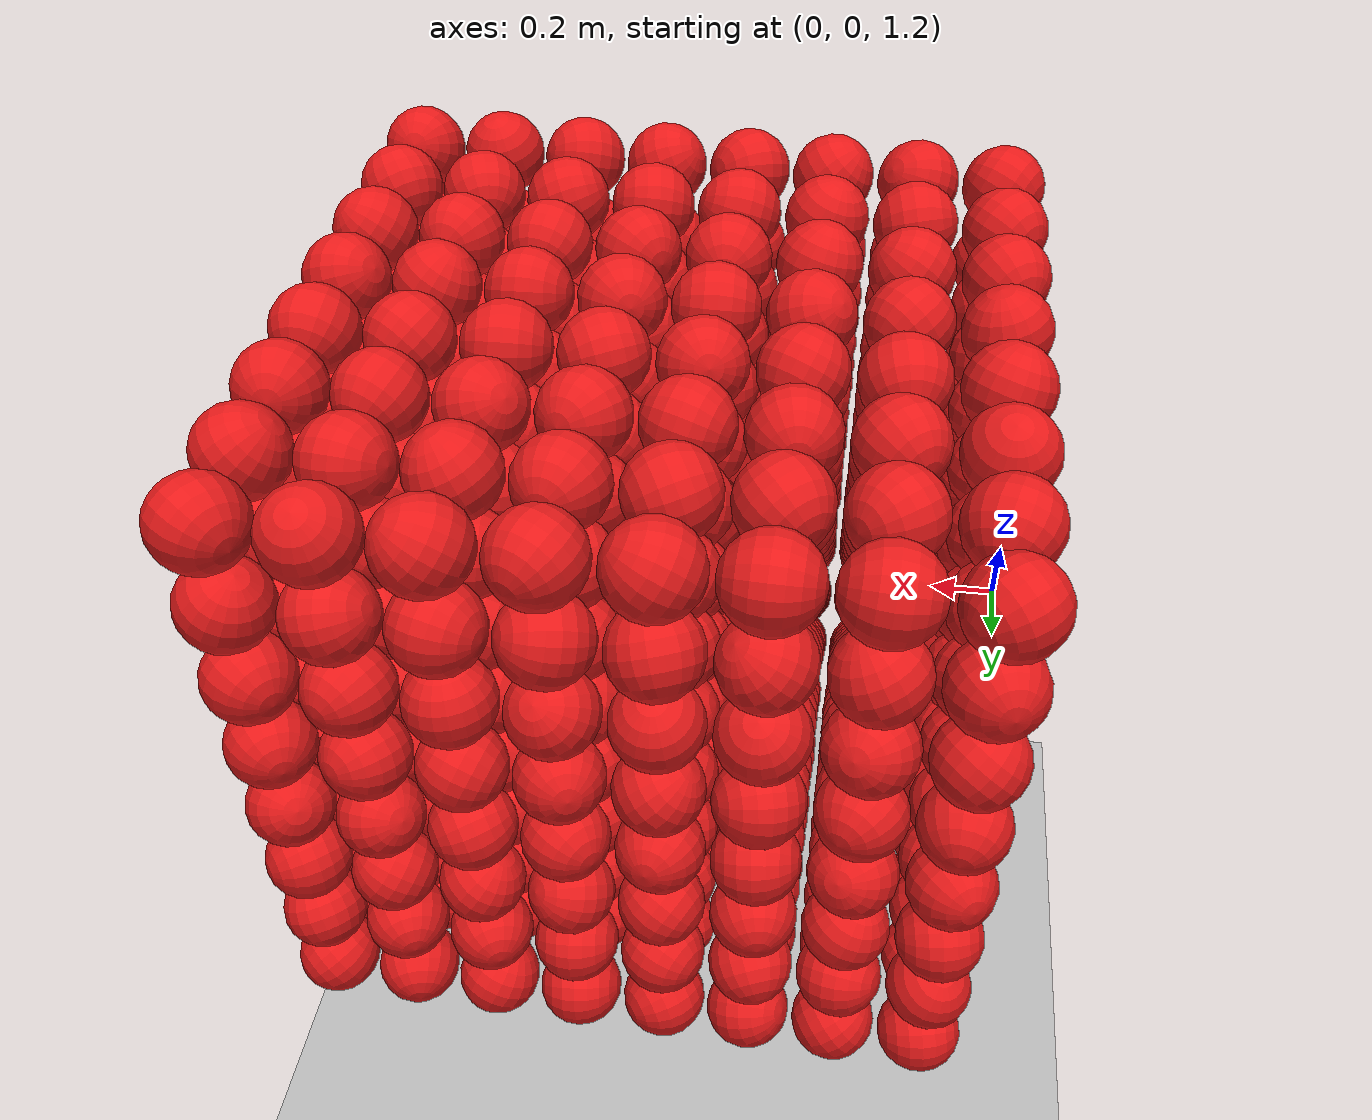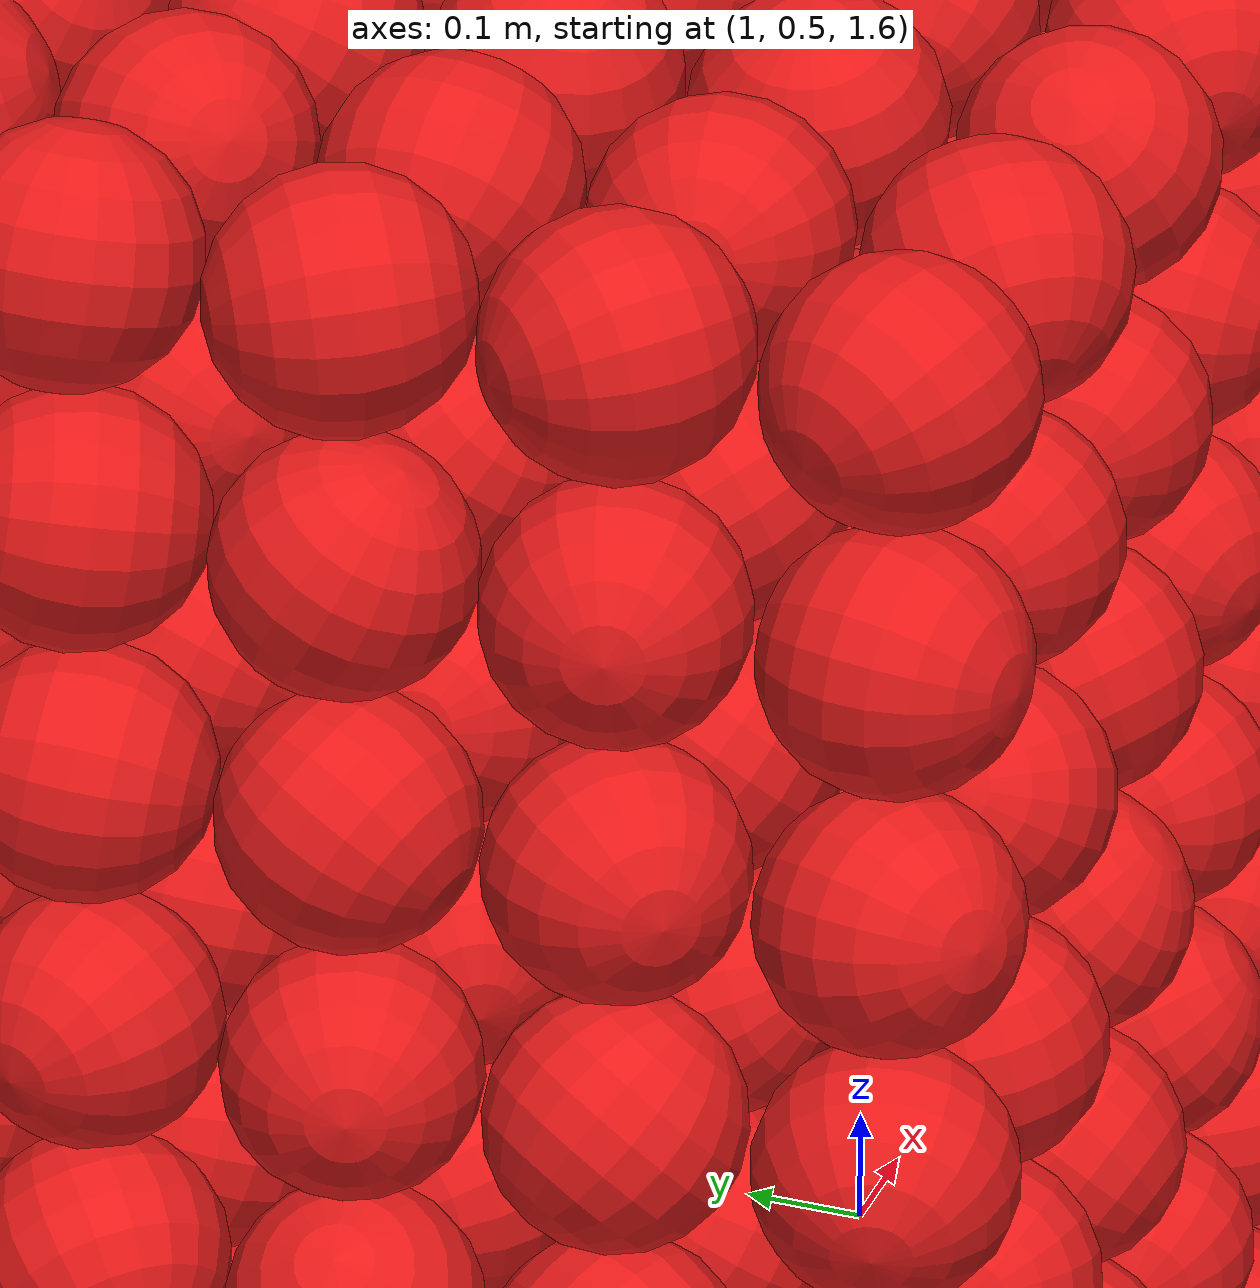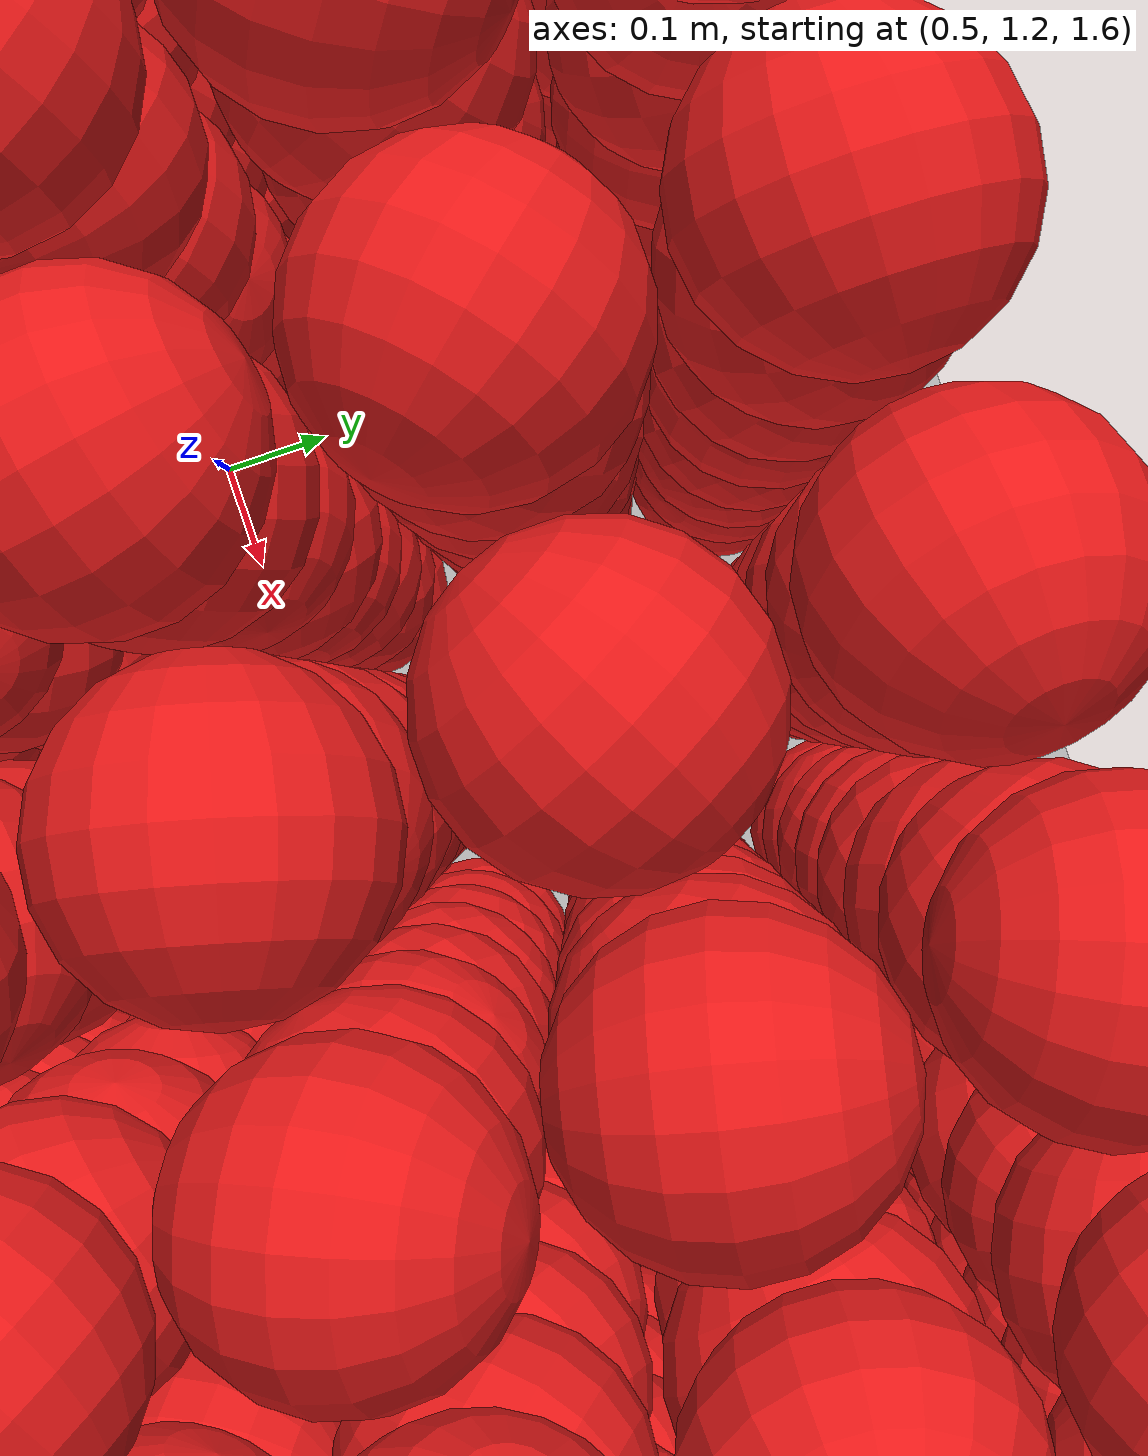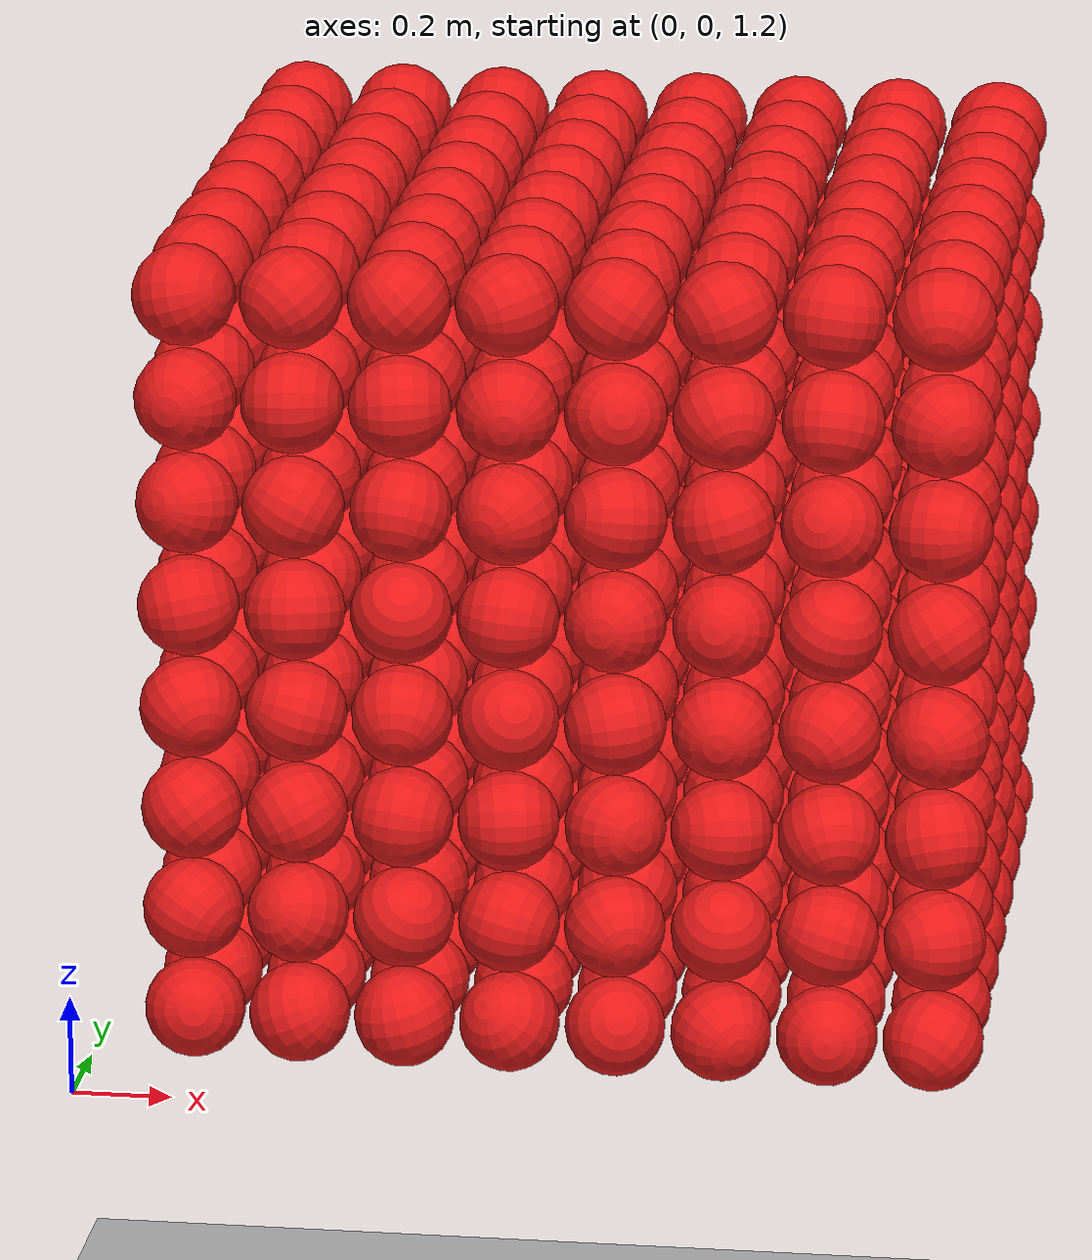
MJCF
<mujoco model="thousand">
    <compiler angle="degree"/>

    <option jacobian="sparse" cone="elliptic"/>

    <size njmax="5000" nconmax="2000" nstack="1000000000"/>

    <default>
        <geom solimp=".9 .9 .01"/>

        <default class="object5">
			<geom type="sphere" material="geom" rgba=".9 .1 .1 1" size="0.100000"/>
        </default>
    </default>

    <asset>
        <texture type="skybox" builtin="gradient" width="128" height="128" rgb1=".4 .6 .8" rgb2="0 0 0"/>
        <texture name="texgeom" type="cube" builtin="flat" mark="cross" width="128" height="128"
            rgb1="0.6 0.6 0.6" rgb2="0.6 0.6 0.6" markrgb="1 1 1"/>
        <texture name="texplane" type="2d" builtin="checker" rgb1=".4 .4 .4" rgb2=".6 .6 .6"
            width="512" height="512"/>
        <material name='geom' texture="texgeom" texuniform="true"/>
        <material name='MatPlane' reflectance='0.3' texture="texplane" texrepeat="1 1" texuniform="true"/>
    </asset>

    <visual>
        <quality shadowsize="4096" offsamples="8"/>
        <map znear="0.1" force="0.05"/>
    </visual>

    <statistic extent="4"/>

    <worldbody>
        <light directional="true" diffuse=".8 .8 .8" pos="0 0 10" dir="0 0 -10"/>

        <geom pos="0 0 0" type="plane" size="200 200 5" rgba=".7 .7 .7 1" material="MatPlane"/>
		<body pos="0.210795 0.210574 1.311362" quat="-0.482607 0.550586 0.572857 0.368485"><inertial pos="0 0 0" mass="1500.000000" diaginertia="6.000000 6.000000 6.000000"/> <freejoint/> <geom class="object5"/> </body>
		<body pos="0.210362 0.210496 1.521659" quat="-0.438105 -0.741014 -0.398316 -0.316712"><inertial pos="0 0 0" mass="1500.000000" diaginertia="6.000000 6.000000 6.000000"/> <freejoint/> <geom class="object5"/> </body>
		<body pos="0.210140 0.210216 1.731556" quat="-0.712424 -0.131189 0.335850 0.602035"><inertial pos="0 0 0" mass="1500.000000" diaginertia="6.000000 6.000000 6.000000"/> <freejoint/> <geom class="object5"/> </body>
		<body pos="0.210601 0.210465 1.941815" quat="-0.396216 -0.275342 -0.806318 0.342126"><inertial pos="0 0 0" mass="1500.000000" diaginertia="6.000000 6.000000 6.000000"/> <freejoint/> <geom class="object5"/> </body>
		<body pos="0.210025 0.210234 2.151979" quat="0.526483 0.571692 -0.514616 -0.362153"><inertial pos="0 0 0" mass="1500.000000" diaginertia="6.000000 6.000000 6.000000"/> <freejoint/> <geom class="object5"/> </body>
		<body pos="0.210423 0.210537 2.361463" quat="0.330379 0.006716 0.765607 0.551952"><inertial pos="0 0 0" mass="1500.000000" diaginertia="6.000000 6.000000 6.000000"/> <freejoint/> <geom class="object5"/> </body>
		<body pos="0.210569 0.210157 2.571626" quat="0.567909 0.644412 0.297634 -0.416685"><inertial pos="0 0 0" mass="1500.000000" diaginertia="6.000000 6.000000 6.000000"/> <freejoint/> <geom class="object5"/> </body>
		<body pos="0.210860 0.210129 2.781743" quat="-0.585136 0.193741 -0.570047 0.543256"><inertial pos="0 0 0" mass="1500.000000" diaginertia="6.000000 6.000000 6.000000"/> <freejoint/> <geom class="object5"/> </body>
		<body pos="0.210172 0.420088 1.311305" quat="0.230490 -0.396998 0.637775 -0.618474"><inertial pos="0 0 0" mass="1500.000000" diaginertia="6.000000 6.000000 6.000000"/> <freejoint/> <geom class="object5"/> </body>
		<body pos="0.210492 0.420641 1.521405" quat="-0.793647 0.233546 -0.511430 0.232421"><inertial pos="0 0 0" mass="1500.000000" diaginertia="6.000000 6.000000 6.000000"/> <freejoint/> <geom class="object5"/> </body>
		<body pos="0.210395 0.420796 1.731879" quat="0.731919 0.529143 -0.207305 0.375935"><inertial pos="0 0 0" mass="1500.000000" diaginertia="6.000000 6.000000 6.000000"/> <freejoint/> <geom class="object5"/> </body>
		<body pos="0.210078 0.420381 1.941438" quat="-0.214260 -0.520895 -0.618609 0.547800"><inertial pos="0 0 0" mass="1500.000000" diaginertia="6.000000 6.000000 6.000000"/> <freejoint/> <geom class="object5"/> </body>
		<body pos="0.210879 0.420772 2.151036" quat="0.185790 0.301602 -0.868166 -0.347571"><inertial pos="0 0 0" mass="1500.000000" diaginertia="6.000000 6.000000 6.000000"/> <freejoint/> <geom class="object5"/> </body>
		<body pos="0.210807 0.420302 2.361490" quat="0.594476 -0.105719 0.704275 0.373387"><inertial pos="0 0 0" mass="1500.000000" diaginertia="6.000000 6.000000 6.000000"/> <freejoint/> <geom class="object5"/> </body>
		<body pos="0.210087 0.420981 2.571566" quat="-0.358398 -0.495802 -0.536368 -0.581412"><inertial pos="0 0 0" mass="1500.000000" diaginertia="6.000000 6.000000 6.000000"/> <freejoint/> <geom class="object5"/> </body>
		<body pos="0.210334 0.420557 2.781846" quat="0.307127 0.241971 -0.701133 -0.596268"><inertial pos="0 0 0" mass="1500.000000" diaginertia="6.000000 6.000000 6.000000"/> <freejoint/> <geom class="object5"/> </body>
		<body pos="0.210652 0.630329 1.311523" quat="-0.596454 -0.075182 0.782904 -0.160160"><inertial pos="0 0 0" mass="1500.000000" diaginertia="6.000000 6.000000 6.000000"/> <freejoint/> <geom class="object5"/> </body>
		<body pos="0.210062 0.630293 1.521552" quat="0.733298 -0.554554 -0.018756 0.392927"><inertial pos="0 0 0" mass="1500.000000" diaginertia="6.000000 6.000000 6.000000"/> <freejoint/> <geom class="object5"/> </body>
		<body pos="0.210753 0.630694 1.731137" quat="0.628023 -0.186917 0.045713 0.754029"><inertial pos="0 0 0" mass="1500.000000" diaginertia="6.000000 6.000000 6.000000"/> <freejoint/> <geom class="object5"/> </body>
		<body pos="0.210958 0.630818 1.941424" quat="0.791305 -0.138126 -0.297980 0.515718"><inertial pos="0 0 0" mass="1500.000000" diaginertia="6.000000 6.000000 6.000000"/> <freejoint/> <geom class="object5"/> </body>
		<body pos="0.210239 0.630176 2.151238" quat="-0.320373 -0.680028 0.076118 0.655080"><inertial pos="0 0 0" mass="1500.000000" diaginertia="6.000000 6.000000 6.000000"/> <freejoint/> <geom class="object5"/> </body>
		<body pos="0.210788 0.630241 2.361696" quat="-0.800250 0.443339 -0.277524 -0.293311"><inertial pos="0 0 0" mass="1500.000000" diaginertia="6.000000 6.000000 6.000000"/> <freejoint/> <geom class="object5"/> </body>
		<body pos="0.210765 0.630384 2.571219" quat="0.139535 -0.615606 -0.743405 -0.221151"><inertial pos="0 0 0" mass="1500.000000" diaginertia="6.000000 6.000000 6.000000"/> <freejoint/> <geom class="object5"/> </body>
		<body pos="0.210020 0.630423 2.781003" quat="-0.716897 -0.489665 -0.470429 0.158062"><inertial pos="0 0 0" mass="1500.000000" diaginertia="6.000000 6.000000 6.000000"/> <freejoint/> <geom class="object5"/> </body>
		<body pos="0.210232 0.840567 1.311551" quat="-0.226102 0.683807 -0.490800 0.490307"><inertial pos="0 0 0" mass="1500.000000" diaginertia="6.000000 6.000000 6.000000"/> <freejoint/> <geom class="object5"/> </body>
		<body pos="0.210787 0.840524 1.521019" quat="-0.361428 0.761808 0.321690 -0.430737"><inertial pos="0 0 0" mass="1500.000000" diaginertia="6.000000 6.000000 6.000000"/> <freejoint/> <geom class="object5"/> </body>
		<body pos="0.210642 0.840121 1.731557" quat="0.553010 -0.164189 -0.799525 0.167278"><inertial pos="0 0 0" mass="1500.000000" diaginertia="6.000000 6.000000 6.000000"/> <freejoint/> <geom class="object5"/> </body>
		<body pos="0.210639 0.840125 1.941865" quat="-0.036243 -0.664531 -0.559344 0.494186"><inertial pos="0 0 0" mass="1500.000000" diaginertia="6.000000 6.000000 6.000000"/> <freejoint/> <geom class="object5"/> </body>
		<body pos="0.210500 0.840444 2.151326" quat="0.100289 -0.737489 0.080375 0.663017"><inertial pos="0 0 0" mass="1500.000000" diaginertia="6.000000 6.000000 6.000000"/> <freejoint/> <geom class="object5"/> </body>
		<body pos="0.210482 0.840328 2.361803" quat="-0.641551 -0.758229 -0.098233 -0.062061"><inertial pos="0 0 0" mass="1500.000000" diaginertia="6.000000 6.000000 6.000000"/> <freejoint/> <geom class="object5"/> </body>
		<body pos="0.210737 0.840699 2.571533" quat="-0.629895 -0.735757 -0.209682 -0.133891"><inertial pos="0 0 0" mass="1500.000000" diaginertia="6.000000 6.000000 6.000000"/> <freejoint/> <geom class="object5"/> </body>
		<body pos="0.210975 0.840927 2.781308" quat="0.719151 0.119456 0.087592 0.678882"><inertial pos="0 0 0" mass="1500.000000" diaginertia="6.000000 6.000000 6.000000"/> <freejoint/> <geom class="object5"/> </body>
		<body pos="0.210788 1.050536 1.311002" quat="-0.321175 -0.158004 0.329473 -0.873687"><inertial pos="0 0 0" mass="1500.000000" diaginertia="6.000000 6.000000 6.000000"/> <freejoint/> <geom class="object5"/> </body>
		<body pos="0.210565 1.050403 1.521054" quat="-0.871282 -0.262069 -0.101592 -0.402326"><inertial pos="0 0 0" mass="1500.000000" diaginertia="6.000000 6.000000 6.000000"/> <freejoint/> <geom class="object5"/> </body>
		<body pos="0.210857 1.050607 1.731197" quat="-0.717610 0.538249 0.307439 -0.317498"><inertial pos="0 0 0" mass="1500.000000" diaginertia="6.000000 6.000000 6.000000"/> <freejoint/> <geom class="object5"/> </body>
		<body pos="0.210057 1.050420 1.941461" quat="0.058262 0.538961 0.817854 -0.192979"><inertial pos="0 0 0" mass="1500.000000" diaginertia="6.000000 6.000000 6.000000"/> <freejoint/> <geom class="object5"/> </body>
		<body pos="0.210190 1.050992 2.151680" quat="0.881080 0.276361 0.301269 -0.237823"><inertial pos="0 0 0" mass="1500.000000" diaginertia="6.000000 6.000000 6.000000"/> <freejoint/> <geom class="object5"/> </body>
		<body pos="0.210028 1.050593 2.361731" quat="0.241789 -0.691680 -0.547862 0.403687"><inertial pos="0 0 0" mass="1500.000000" diaginertia="6.000000 6.000000 6.000000"/> <freejoint/> <geom class="object5"/> </body>
		<body pos="0.210496 1.050384 2.571288" quat="-0.473315 0.675092 -0.153847 -0.544568"><inertial pos="0 0 0" mass="1500.000000" diaginertia="6.000000 6.000000 6.000000"/> <freejoint/> <geom class="object5"/> </body>
		<body pos="0.210541 1.050031 2.781548" quat="-0.235075 0.593183 -0.766560 -0.072515"><inertial pos="0 0 0" mass="1500.000000" diaginertia="6.000000 6.000000 6.000000"/> <freejoint/> <geom class="object5"/> </body>
		<body pos="0.210594 1.260085 1.311497" quat="0.461355 -0.610114 0.333555 0.551048"><inertial pos="0 0 0" mass="1500.000000" diaginertia="6.000000 6.000000 6.000000"/> <freejoint/> <geom class="object5"/> </body>
		<body pos="0.210513 1.260005 1.521357" quat="0.709216 -0.532776 0.411965 -0.208438"><inertial pos="0 0 0" mass="1500.000000" diaginertia="6.000000 6.000000 6.000000"/> <freejoint/> <geom class="object5"/> </body>
		<body pos="0.210282 1.260543 1.731407" quat="0.658604 -0.224235 -0.607187 -0.383776"><inertial pos="0 0 0" mass="1500.000000" diaginertia="6.000000 6.000000 6.000000"/> <freejoint/> <geom class="object5"/> </body>
		<body pos="0.210156 1.260813 1.941630" quat="0.503012 0.517982 0.149214 -0.675580"><inertial pos="0 0 0" mass="1500.000000" diaginertia="6.000000 6.000000 6.000000"/> <freejoint/> <geom class="object5"/> </body>
		<body pos="0.210097 1.260831 2.151315" quat="0.324124 -0.102478 0.519115 -0.784195"><inertial pos="0 0 0" mass="1500.000000" diaginertia="6.000000 6.000000 6.000000"/> <freejoint/> <geom class="object5"/> </body>
		<body pos="0.210285 1.260691 2.361973" quat="-0.324962 0.529035 0.599776 0.504767"><inertial pos="0 0 0" mass="1500.000000" diaginertia="6.000000 6.000000 6.000000"/> <freejoint/> <geom class="object5"/> </body>
		<body pos="0.210752 1.260259 2.571947" quat="0.618279 0.609805 0.493644 -0.046744"><inertial pos="0 0 0" mass="1500.000000" diaginertia="6.000000 6.000000 6.000000"/> <freejoint/> <geom class="object5"/> </body>
		<body pos="0.210851 1.260929 2.781024" quat="0.420595 -0.061836 0.167428 0.889519"><inertial pos="0 0 0" mass="1500.000000" diaginertia="6.000000 6.000000 6.000000"/> <freejoint/> <geom class="object5"/> </body>
		<body pos="0.210847 1.470977 1.311345" quat="-0.664298 -0.547799 -0.487880 0.143519"><inertial pos="0 0 0" mass="1500.000000" diaginertia="6.000000 6.000000 6.000000"/> <freejoint/> <geom class="object5"/> </body>
		<body pos="0.210285 1.470916 1.521671" quat="0.400429 -0.444616 -0.503692 -0.623111"><inertial pos="0 0 0" mass="1500.000000" diaginertia="6.000000 6.000000 6.000000"/> <freejoint/> <geom class="object5"/> </body>
		<body pos="0.210618 1.470590 1.731375" quat="-0.730967 -0.521755 0.010371 0.439718"><inertial pos="0 0 0" mass="1500.000000" diaginertia="6.000000 6.000000 6.000000"/> <freejoint/> <geom class="object5"/> </body>
		<body pos="0.210762 1.470934 1.941795" quat="-0.112654 -0.383244 -0.904261 0.150818"><inertial pos="0 0 0" mass="1500.000000" diaginertia="6.000000 6.000000 6.000000"/> <freejoint/> <geom class="object5"/> </body>
		<body pos="0.210208 1.470118 2.151768" quat="-0.093011 0.491427 -0.855752 -0.132427"><inertial pos="0 0 0" mass="1500.000000" diaginertia="6.000000 6.000000 6.000000"/> <freejoint/> <geom class="object5"/> </body>
		<body pos="0.210557 1.470856 2.361912" quat="-0.315928 -0.271234 -0.845263 0.334891"><inertial pos="0 0 0" mass="1500.000000" diaginertia="6.000000 6.000000 6.000000"/> <freejoint/> <geom class="object5"/> </body>
		<body pos="0.210219 1.470866 2.571393" quat="-0.075661 -0.522145 -0.709702 0.466865"><inertial pos="0 0 0" mass="1500.000000" diaginertia="6.000000 6.000000 6.000000"/> <freejoint/> <geom class="object5"/> </body>
		<body pos="0.210802 1.470463 2.781852" quat="0.182161 -0.463216 -0.681293 -0.536738"><inertial pos="0 0 0" mass="1500.000000" diaginertia="6.000000 6.000000 6.000000"/> <freejoint/> <geom class="object5"/> </body>
		<body pos="0.210316 1.680732 1.311773" quat="-0.577649 0.486207 -0.550073 0.356853"><inertial pos="0 0 0" mass="1500.000000" diaginertia="6.000000 6.000000 6.000000"/> <freejoint/> <geom class="object5"/> </body>
		<body pos="0.210079 1.680394 1.521816" quat="0.061092 0.911754 -0.373622 0.159308"><inertial pos="0 0 0" mass="1500.000000" diaginertia="6.000000 6.000000 6.000000"/> <freejoint/> <geom class="object5"/> </body>
		<body pos="0.210190 1.680392 1.731999" quat="-0.232615 0.608014 0.294157 -0.699772"><inertial pos="0 0 0" mass="1500.000000" diaginertia="6.000000 6.000000 6.000000"/> <freejoint/> <geom class="object5"/> </body>
		<body pos="0.210481 1.680677 1.941402" quat="-0.472370 0.083530 0.613594 0.627209"><inertial pos="0 0 0" mass="1500.000000" diaginertia="6.000000 6.000000 6.000000"/> <freejoint/> <geom class="object5"/> </body>
		<body pos="0.210990 1.680836 2.151654" quat="0.550778 0.542720 0.390772 -0.499396"><inertial pos="0 0 0" mass="1500.000000" diaginertia="6.000000 6.000000 6.000000"/> <freejoint/> <geom class="object5"/> </body>
		<body pos="0.210079 1.680509 2.361093" quat="-0.113561 -0.343617 -0.220848 0.905681"><inertial pos="0 0 0" mass="1500.000000" diaginertia="6.000000 6.000000 6.000000"/> <freejoint/> <geom class="object5"/> </body>
		<body pos="0.210869 1.680948 2.571254" quat="-0.753756 0.553978 0.315062 0.160301"><inertial pos="0 0 0" mass="1500.000000" diaginertia="6.000000 6.000000 6.000000"/> <freejoint/> <geom class="object5"/> </body>
		<body pos="0.210215 1.680535 2.781056" quat="-0.121585 -0.545339 -0.303694 0.771746"><inertial pos="0 0 0" mass="1500.000000" diaginertia="6.000000 6.000000 6.000000"/> <freejoint/> <geom class="object5"/> </body>
		<body pos="0.420847 0.210257 1.311377" quat="0.348054 0.420656 -0.727907 -0.414798"><inertial pos="0 0 0" mass="1500.000000" diaginertia="6.000000 6.000000 6.000000"/> <freejoint/> <geom class="object5"/> </body>
		<body pos="0.420067 0.210706 1.521876" quat="-0.461300 0.399701 -0.748359 -0.259616"><inertial pos="0 0 0" mass="1500.000000" diaginertia="6.000000 6.000000 6.000000"/> <freejoint/> <geom class="object5"/> </body>
		<body pos="0.420836 0.210696 1.731695" quat="0.736169 -0.427941 0.314516 -0.419525"><inertial pos="0 0 0" mass="1500.000000" diaginertia="6.000000 6.000000 6.000000"/> <freejoint/> <geom class="object5"/> </body>
		<body pos="0.420945 0.210781 1.941825" quat="0.440510 0.547731 -0.176892 -0.688949"><inertial pos="0 0 0" mass="1500.000000" diaginertia="6.000000 6.000000 6.000000"/> <freejoint/> <geom class="object5"/> </body>
		<body pos="0.420160 0.210817 2.151031" quat="0.079110 0.581746 0.806355 -0.071449"><inertial pos="0 0 0" mass="1500.000000" diaginertia="6.000000 6.000000 6.000000"/> <freejoint/> <geom class="object5"/> </body>
		<body pos="0.420070 0.210522 2.361196" quat="-0.298162 0.704660 -0.495756 0.410829"><inertial pos="0 0 0" mass="1500.000000" diaginertia="6.000000 6.000000 6.000000"/> <freejoint/> <geom class="object5"/> </body>
		<body pos="0.420341 0.210474 2.571100" quat="-0.543456 0.446955 -0.530247 0.472996"><inertial pos="0 0 0" mass="1500.000000" diaginertia="6.000000 6.000000 6.000000"/> <freejoint/> <geom class="object5"/> </body>
		<body pos="0.420394 0.210440 2.781351" quat="-0.838653 0.404516 -0.262743 0.252969"><inertial pos="0 0 0" mass="1500.000000" diaginertia="6.000000 6.000000 6.000000"/> <freejoint/> <geom class="object5"/> </body>
		<body pos="0.420772 0.420677 1.311486" quat="0.439621 -0.597191 -0.664323 -0.093653"><inertial pos="0 0 0" mass="1500.000000" diaginertia="6.000000 6.000000 6.000000"/> <freejoint/> <geom class="object5"/> </body>
		<body pos="0.420143 0.420808 1.521002" quat="-0.603565 -0.117079 -0.395949 0.682075"><inertial pos="0 0 0" mass="1500.000000" diaginertia="6.000000 6.000000 6.000000"/> <freejoint/> <geom class="object5"/> </body>
		<body pos="0.420371 0.420491 1.731268" quat="0.149204 0.039209 0.936668 0.314409"><inertial pos="0 0 0" mass="1500.000000" diaginertia="6.000000 6.000000 6.000000"/> <freejoint/> <geom class="object5"/> </body>
		<body pos="0.420846 0.420087 1.941423" quat="-0.826785 0.184131 0.417268 0.329256"><inertial pos="0 0 0" mass="1500.000000" diaginertia="6.000000 6.000000 6.000000"/> <freejoint/> <geom class="object5"/> </body>
		<body pos="0.420061 0.420677 2.151307" quat="-0.281736 0.420635 -0.729674 -0.459637"><inertial pos="0 0 0" mass="1500.000000" diaginertia="6.000000 6.000000 6.000000"/> <freejoint/> <geom class="object5"/> </body>
		<body pos="0.420439 0.420587 2.361307" quat="-0.132203 -0.388558 0.852181 0.324549"><inertial pos="0 0 0" mass="1500.000000" diaginertia="6.000000 6.000000 6.000000"/> <freejoint/> <geom class="object5"/> </body>
		<body pos="0.420177 0.420645 2.571035" quat="0.463884 -0.817762 -0.189562 0.283096"><inertial pos="0 0 0" mass="1500.000000" diaginertia="6.000000 6.000000 6.000000"/> <freejoint/> <geom class="object5"/> </body>
		<body pos="0.420039 0.420435 2.781174" quat="0.162572 -0.603630 -0.227336 0.746672"><inertial pos="0 0 0" mass="1500.000000" diaginertia="6.000000 6.000000 6.000000"/> <freejoint/> <geom class="object5"/> </body>
		<body pos="0.420002 0.630680 1.311283" quat="0.534756 -0.342559 -0.182850 0.750503"><inertial pos="0 0 0" mass="1500.000000" diaginertia="6.000000 6.000000 6.000000"/> <freejoint/> <geom class="object5"/> </body>
		<body pos="0.420835 0.630890 1.521933" quat="-0.787202 -0.322225 0.453687 0.265805"><inertial pos="0 0 0" mass="1500.000000" diaginertia="6.000000 6.000000 6.000000"/> <freejoint/> <geom class="object5"/> </body>
		<body pos="0.420834 0.630221 1.731319" quat="-0.455394 -0.765927 0.292453 -0.347048"><inertial pos="0 0 0" mass="1500.000000" diaginertia="6.000000 6.000000 6.000000"/> <freejoint/> <geom class="object5"/> </body>
		<body pos="0.420031 0.630284 1.941113" quat="-0.579087 0.109518 -0.661092 0.464351"><inertial pos="0 0 0" mass="1500.000000" diaginertia="6.000000 6.000000 6.000000"/> <freejoint/> <geom class="object5"/> </body>
		<body pos="0.420066 0.630484 2.151162" quat="-0.127230 0.591890 0.254992 0.753962"><inertial pos="0 0 0" mass="1500.000000" diaginertia="6.000000 6.000000 6.000000"/> <freejoint/> <geom class="object5"/> </body>
		<body pos="0.420396 0.630412 2.361779" quat="0.699052 0.294384 -0.571383 -0.313346"><inertial pos="0 0 0" mass="1500.000000" diaginertia="6.000000 6.000000 6.000000"/> <freejoint/> <geom class="object5"/> </body>
		<body pos="0.420271 0.630231 2.571702" quat="-0.298814 0.743185 0.568420 0.187844"><inertial pos="0 0 0" mass="1500.000000" diaginertia="6.000000 6.000000 6.000000"/> <freejoint/> <geom class="object5"/> </body>
		<body pos="0.420879 0.630307 2.781626" quat="0.286781 -0.425522 0.177556 -0.839739"><inertial pos="0 0 0" mass="1500.000000" diaginertia="6.000000 6.000000 6.000000"/> <freejoint/> <geom class="object5"/> </body>
		<body pos="0.420798 0.840875 1.311648" quat="-0.552453 0.544545 -0.548862 -0.311477"><inertial pos="0 0 0" mass="1500.000000" diaginertia="6.000000 6.000000 6.000000"/> <freejoint/> <geom class="object5"/> </body>
		<body pos="0.420375 0.840414 1.521165" quat="0.683153 -0.574928 0.394751 0.216636"><inertial pos="0 0 0" mass="1500.000000" diaginertia="6.000000 6.000000 6.000000"/> <freejoint/> <geom class="object5"/> </body>
		<body pos="0.420307 0.840116 1.731956" quat="0.663189 -0.711585 -0.219141 -0.076185"><inertial pos="0 0 0" mass="1500.000000" diaginertia="6.000000 6.000000 6.000000"/> <freejoint/> <geom class="object5"/> </body>
		<body pos="0.420738 0.840876 1.941974" quat="0.504235 0.276839 0.770491 -0.274684"><inertial pos="0 0 0" mass="1500.000000" diaginertia="6.000000 6.000000 6.000000"/> <freejoint/> <geom class="object5"/> </body>
		<body pos="0.420899 0.840789 2.151909" quat="-0.129313 -0.706565 0.670546 0.185503"><inertial pos="0 0 0" mass="1500.000000" diaginertia="6.000000 6.000000 6.000000"/> <freejoint/> <geom class="object5"/> </body>
		<body pos="0.420750 0.840580 2.361995" quat="-0.501845 0.313638 -0.500590 -0.631817"><inertial pos="0 0 0" mass="1500.000000" diaginertia="6.000000 6.000000 6.000000"/> <freejoint/> <geom class="object5"/> </body>
		<body pos="0.420634 0.840551 2.571772" quat="-0.643155 -0.655061 0.119219 0.378198"><inertial pos="0 0 0" mass="1500.000000" diaginertia="6.000000 6.000000 6.000000"/> <freejoint/> <geom class="object5"/> </body>
		<body pos="0.420185 0.840536 2.781574" quat="0.170728 -0.747098 -0.373993 -0.522327"><inertial pos="0 0 0" mass="1500.000000" diaginertia="6.000000 6.000000 6.000000"/> <freejoint/> <geom class="object5"/> </body>
		<body pos="0.420528 1.050735 1.311918" quat="-0.702040 0.484902 0.519565 -0.045413"><inertial pos="0 0 0" mass="1500.000000" diaginertia="6.000000 6.000000 6.000000"/> <freejoint/> <geom class="object5"/> </body>
		<body pos="0.420370 1.050076 1.521170" quat="0.657898 0.344814 0.641920 -0.190295"><inertial pos="0 0 0" mass="1500.000000" diaginertia="6.000000 6.000000 6.000000"/> <freejoint/> <geom class="object5"/> </body>
		<body pos="0.420792 1.050456 1.731894" quat="-0.746003 0.236371 0.538627 -0.312231"><inertial pos="0 0 0" mass="1500.000000" diaginertia="6.000000 6.000000 6.000000"/> <freejoint/> <geom class="object5"/> </body>
		<body pos="0.420536 1.050866 1.941534" quat="0.596333 0.175142 0.774850 -0.115410"><inertial pos="0 0 0" mass="1500.000000" diaginertia="6.000000 6.000000 6.000000"/> <freejoint/> <geom class="object5"/> </body>
		<body pos="0.420093 1.050929 2.151419" quat="0.052270 0.373773 -0.871761 -0.312399"><inertial pos="0 0 0" mass="1500.000000" diaginertia="6.000000 6.000000 6.000000"/> <freejoint/> <geom class="object5"/> </body>
		<body pos="0.420793 1.050007 2.361054" quat="-0.454436 -0.286672 0.565328 -0.625868"><inertial pos="0 0 0" mass="1500.000000" diaginertia="6.000000 6.000000 6.000000"/> <freejoint/> <geom class="object5"/> </body>
		<body pos="0.420406 1.050694 2.571829" quat="0.076892 0.686639 0.695448 0.197400"><inertial pos="0 0 0" mass="1500.000000" diaginertia="6.000000 6.000000 6.000000"/> <freejoint/> <geom class="object5"/> </body>
		<body pos="0.420910 1.050894 2.781345" quat="0.703911 0.553424 -0.193119 0.401168"><inertial pos="0 0 0" mass="1500.000000" diaginertia="6.000000 6.000000 6.000000"/> <freejoint/> <geom class="object5"/> </body>
		<body pos="0.420328 1.260157 1.311739" quat="0.349573 0.265101 -0.688437 -0.577559"><inertial pos="0 0 0" mass="1500.000000" diaginertia="6.000000 6.000000 6.000000"/> <freejoint/> <geom class="object5"/> </body>
		<body pos="0.420799 1.260587 1.521302" quat="-0.585311 -0.788865 0.015622 0.186704"><inertial pos="0 0 0" mass="1500.000000" diaginertia="6.000000 6.000000 6.000000"/> <freejoint/> <geom class="object5"/> </body>
		<body pos="0.420069 1.260164 1.731511" quat="0.080956 0.019559 -0.736847 -0.670910"><inertial pos="0 0 0" mass="1500.000000" diaginertia="6.000000 6.000000 6.000000"/> <freejoint/> <geom class="object5"/> </body>
		<body pos="0.420409 1.260694 1.941781" quat="0.271892 0.163110 0.946561 0.059095"><inertial pos="0 0 0" mass="1500.000000" diaginertia="6.000000 6.000000 6.000000"/> <freejoint/> <geom class="object5"/> </body>
		<body pos="0.420288 1.260196 2.151215" quat="-0.134470 0.144422 0.896483 -0.396709"><inertial pos="0 0 0" mass="1500.000000" diaginertia="6.000000 6.000000 6.000000"/> <freejoint/> <geom class="object5"/> </body>
		<body pos="0.420281 1.260619 2.361220" quat="-0.427257 -0.629955 0.021278 -0.648194"><inertial pos="0 0 0" mass="1500.000000" diaginertia="6.000000 6.000000 6.000000"/> <freejoint/> <geom class="object5"/> </body>
		<body pos="0.420556 1.260556 2.571074" quat="-0.327017 0.863467 0.230092 -0.307477"><inertial pos="0 0 0" mass="1500.000000" diaginertia="6.000000 6.000000 6.000000"/> <freejoint/> <geom class="object5"/> </body>
		<body pos="0.420523 1.260392 2.781067" quat="0.685188 0.650232 0.168591 0.281591"><inertial pos="0 0 0" mass="1500.000000" diaginertia="6.000000 6.000000 6.000000"/> <freejoint/> <geom class="object5"/> </body>
		<body pos="0.420589 1.470617 1.311240" quat="0.519174 0.366790 0.424274 -0.644915"><inertial pos="0 0 0" mass="1500.000000" diaginertia="6.000000 6.000000 6.000000"/> <freejoint/> <geom class="object5"/> </body>
		<body pos="0.420005 1.470739 1.521811" quat="0.099758 -0.684845 -0.272668 0.668347"><inertial pos="0 0 0" mass="1500.000000" diaginertia="6.000000 6.000000 6.000000"/> <freejoint/> <geom class="object5"/> </body>
		<body pos="0.420853 1.470687 1.731167" quat="0.387979 -0.907907 0.131736 -0.088448"><inertial pos="0 0 0" mass="1500.000000" diaginertia="6.000000 6.000000 6.000000"/> <freejoint/> <geom class="object5"/> </body>
		<body pos="0.420665 1.470434 1.941031" quat="-0.114526 -0.065491 -0.973646 0.186033"><inertial pos="0 0 0" mass="1500.000000" diaginertia="6.000000 6.000000 6.000000"/> <freejoint/> <geom class="object5"/> </body>
		<body pos="0.420302 1.470826 2.151916" quat="-0.415964 -0.364714 -0.728642 0.403779"><inertial pos="0 0 0" mass="1500.000000" diaginertia="6.000000 6.000000 6.000000"/> <freejoint/> <geom class="object5"/> </body>
		<body pos="0.420717 1.470621 2.361376" quat="0.309926 0.041001 0.356258 0.880537"><inertial pos="0 0 0" mass="1500.000000" diaginertia="6.000000 6.000000 6.000000"/> <freejoint/> <geom class="object5"/> </body>
		<body pos="0.420331 1.470558 2.571029" quat="-0.441746 0.451959 -0.330906 -0.700782"><inertial pos="0 0 0" mass="1500.000000" diaginertia="6.000000 6.000000 6.000000"/> <freejoint/> <geom class="object5"/> </body>
		<body pos="0.420699 1.470638 2.781648" quat="0.697774 -0.612653 0.303962 -0.213013"><inertial pos="0 0 0" mass="1500.000000" diaginertia="6.000000 6.000000 6.000000"/> <freejoint/> <geom class="object5"/> </body>
		<body pos="0.420693 1.680304 1.311650" quat="-0.290218 0.853037 -0.229810 0.367816"><inertial pos="0 0 0" mass="1500.000000" diaginertia="6.000000 6.000000 6.000000"/> <freejoint/> <geom class="object5"/> </body>
		<body pos="0.420753 1.680199 1.521678" quat="0.460811 0.358216 -0.514339 -0.628323"><inertial pos="0 0 0" mass="1500.000000" diaginertia="6.000000 6.000000 6.000000"/> <freejoint/> <geom class="object5"/> </body>
		<body pos="0.420818 1.680980 1.731752" quat="0.658205 0.174318 -0.065539 -0.729441"><inertial pos="0 0 0" mass="1500.000000" diaginertia="6.000000 6.000000 6.000000"/> <freejoint/> <geom class="object5"/> </body>
		<body pos="0.420600 1.680781 1.941818" quat="-0.446101 0.375197 0.286039 0.760528"><inertial pos="0 0 0" mass="1500.000000" diaginertia="6.000000 6.000000 6.000000"/> <freejoint/> <geom class="object5"/> </body>
		<body pos="0.420412 1.680051 2.151315" quat="-0.294416 -0.011544 -0.706265 -0.643720"><inertial pos="0 0 0" mass="1500.000000" diaginertia="6.000000 6.000000 6.000000"/> <freejoint/> <geom class="object5"/> </body>
		<body pos="0.420239 1.680782 2.361869" quat="0.220979 -0.298497 -0.407709 -0.834171"><inertial pos="0 0 0" mass="1500.000000" diaginertia="6.000000 6.000000 6.000000"/> <freejoint/> <geom class="object5"/> </body>
		<body pos="0.420869 1.680248 2.571985" quat="-0.768160 0.067972 -0.250413 0.585323"><inertial pos="0 0 0" mass="1500.000000" diaginertia="6.000000 6.000000 6.000000"/> <freejoint/> <geom class="object5"/> </body>
		<body pos="0.420914 1.680361 2.781911" quat="-0.451823 -0.551818 0.479853 0.510973"><inertial pos="0 0 0" mass="1500.000000" diaginertia="6.000000 6.000000 6.000000"/> <freejoint/> <geom class="object5"/> </body>
		<body pos="0.630590 0.210056 1.311882" quat="0.622346 0.122398 -0.070181 -0.769921"><inertial pos="0 0 0" mass="1500.000000" diaginertia="6.000000 6.000000 6.000000"/> <freejoint/> <geom class="object5"/> </body>
		<body pos="0.630383 0.210740 1.521522" quat="-0.005136 0.523259 -0.765754 -0.373891"><inertial pos="0 0 0" mass="1500.000000" diaginertia="6.000000 6.000000 6.000000"/> <freejoint/> <geom class="object5"/> </body>
		<body pos="0.630142 0.210033 1.731289" quat="0.490928 -0.419918 0.609480 -0.459557"><inertial pos="0 0 0" mass="1500.000000" diaginertia="6.000000 6.000000 6.000000"/> <freejoint/> <geom class="object5"/> </body>
		<body pos="0.630467 0.210370 1.941658" quat="0.584203 -0.320786 -0.355270 -0.655428"><inertial pos="0 0 0" mass="1500.000000" diaginertia="6.000000 6.000000 6.000000"/> <freejoint/> <geom class="object5"/> </body>
		<body pos="0.630186 0.210760 2.151910" quat="0.278938 0.033655 0.388822 -0.877427"><inertial pos="0 0 0" mass="1500.000000" diaginertia="6.000000 6.000000 6.000000"/> <freejoint/> <geom class="object5"/> </body>
		<body pos="0.630890 0.210673 2.361165" quat="0.005322 0.066030 0.257325 0.964052"><inertial pos="0 0 0" mass="1500.000000" diaginertia="6.000000 6.000000 6.000000"/> <freejoint/> <geom class="object5"/> </body>
		<body pos="0.630569 0.210578 2.571937" quat="-0.702245 0.254664 -0.641641 0.174054"><inertial pos="0 0 0" mass="1500.000000" diaginertia="6.000000 6.000000 6.000000"/> <freejoint/> <geom class="object5"/> </body>
		<body pos="0.630804 0.210032 2.781522" quat="-0.390482 0.310006 0.188567 -0.846087"><inertial pos="0 0 0" mass="1500.000000" diaginertia="6.000000 6.000000 6.000000"/> <freejoint/> <geom class="object5"/> </body>
		<body pos="0.630891 0.420953 1.311181" quat="-0.607791 0.695552 -0.102750 0.369107"><inertial pos="0 0 0" mass="1500.000000" diaginertia="6.000000 6.000000 6.000000"/> <freejoint/> <geom class="object5"/> </body>
		<body pos="0.630923 0.420872 1.521963" quat="-0.326987 0.337926 0.645315 0.602041"><inertial pos="0 0 0" mass="1500.000000" diaginertia="6.000000 6.000000 6.000000"/> <freejoint/> <geom class="object5"/> </body>
		<body pos="0.630829 0.420035 1.731906" quat="0.456792 0.259210 0.850464 0.029356"><inertial pos="0 0 0" mass="1500.000000" diaginertia="6.000000 6.000000 6.000000"/> <freejoint/> <geom class="object5"/> </body>
		<body pos="0.630865 0.420140 1.941657" quat="0.170279 0.024475 -0.467622 0.867027"><inertial pos="0 0 0" mass="1500.000000" diaginertia="6.000000 6.000000 6.000000"/> <freejoint/> <geom class="object5"/> </body>
		<body pos="0.630916 0.420652 2.151111" quat="0.032755 -0.042431 -0.967038 -0.248925"><inertial pos="0 0 0" mass="1500.000000" diaginertia="6.000000 6.000000 6.000000"/> <freejoint/> <geom class="object5"/> </body>
		<body pos="0.630805 0.420787 2.361120" quat="-0.216442 0.732920 -0.608039 0.215104"><inertial pos="0 0 0" mass="1500.000000" diaginertia="6.000000 6.000000 6.000000"/> <freejoint/> <geom class="object5"/> </body>
		<body pos="0.630037 0.420682 2.571827" quat="0.606473 -0.449682 -0.032924 -0.654898"><inertial pos="0 0 0" mass="1500.000000" diaginertia="6.000000 6.000000 6.000000"/> <freejoint/> <geom class="object5"/> </body>
		<body pos="0.630266 0.420765 2.781584" quat="0.067936 0.864557 0.474250 0.151703"><inertial pos="0 0 0" mass="1500.000000" diaginertia="6.000000 6.000000 6.000000"/> <freejoint/> <geom class="object5"/> </body>
		<body pos="0.630791 0.630549 1.311076" quat="-0.057196 0.778831 -0.215839 -0.586143"><inertial pos="0 0 0" mass="1500.000000" diaginertia="6.000000 6.000000 6.000000"/> <freejoint/> <geom class="object5"/> </body>
		<body pos="0.630541 0.630369 1.521759" quat="0.464613 -0.265418 0.807267 -0.249014"><inertial pos="0 0 0" mass="1500.000000" diaginertia="6.000000 6.000000 6.000000"/> <freejoint/> <geom class="object5"/> </body>
		<body pos="0.630193 0.630091 1.731313" quat="0.783429 0.236671 -0.498865 -0.285238"><inertial pos="0 0 0" mass="1500.000000" diaginertia="6.000000 6.000000 6.000000"/> <freejoint/> <geom class="object5"/> </body>
		<body pos="0.630343 0.630895 1.941504" quat="0.143464 0.667122 -0.343704 -0.645162"><inertial pos="0 0 0" mass="1500.000000" diaginertia="6.000000 6.000000 6.000000"/> <freejoint/> <geom class="object5"/> </body>
		<body pos="0.630823 0.630076 2.151082" quat="-0.431863 0.806824 -0.058334 -0.398907"><inertial pos="0 0 0" mass="1500.000000" diaginertia="6.000000 6.000000 6.000000"/> <freejoint/> <geom class="object5"/> </body>
		<body pos="0.630460 0.630674 2.361574" quat="0.548744 -0.678962 -0.384397 0.300217"><inertial pos="0 0 0" mass="1500.000000" diaginertia="6.000000 6.000000 6.000000"/> <freejoint/> <geom class="object5"/> </body>
		<body pos="0.630432 0.630324 2.571046" quat="-0.545764 -0.211164 0.332592 -0.739550"><inertial pos="0 0 0" mass="1500.000000" diaginertia="6.000000 6.000000 6.000000"/> <freejoint/> <geom class="object5"/> </body>
		<body pos="0.630845 0.630883 2.781928" quat="0.184082 -0.579031 0.793969 0.021220"><inertial pos="0 0 0" mass="1500.000000" diaginertia="6.000000 6.000000 6.000000"/> <freejoint/> <geom class="object5"/> </body>
		<body pos="0.630613 0.840687 1.311084" quat="0.489901 -0.461330 -0.610486 -0.417707"><inertial pos="0 0 0" mass="1500.000000" diaginertia="6.000000 6.000000 6.000000"/> <freejoint/> <geom class="object5"/> </body>
		<body pos="0.630282 0.840251 1.521124" quat="0.440304 -0.580308 -0.661020 0.180075"><inertial pos="0 0 0" mass="1500.000000" diaginertia="6.000000 6.000000 6.000000"/> <freejoint/> <geom class="object5"/> </body>
		<body pos="0.630051 0.840823 1.731037" quat="-0.632520 -0.537385 0.440928 0.341641"><inertial pos="0 0 0" mass="1500.000000" diaginertia="6.000000 6.000000 6.000000"/> <freejoint/> <geom class="object5"/> </body>
		<body pos="0.630712 0.840276 1.941996" quat="-0.345777 0.002193 -0.637094 0.688872"><inertial pos="0 0 0" mass="1500.000000" diaginertia="6.000000 6.000000 6.000000"/> <freejoint/> <geom class="object5"/> </body>
		<body pos="0.630238 0.840067 2.151366" quat="0.806959 -0.475218 -0.350611 0.007573"><inertial pos="0 0 0" mass="1500.000000" diaginertia="6.000000 6.000000 6.000000"/> <freejoint/> <geom class="object5"/> </body>
		<body pos="0.630631 0.840393 2.361680" quat="-0.507635 -0.589681 -0.623784 0.073995"><inertial pos="0 0 0" mass="1500.000000" diaginertia="6.000000 6.000000 6.000000"/> <freejoint/> <geom class="object5"/> </body>
		<body pos="0.630891 0.840586 2.571532" quat="0.459717 -0.295201 -0.761594 0.348555"><inertial pos="0 0 0" mass="1500.000000" diaginertia="6.000000 6.000000 6.000000"/> <freejoint/> <geom class="object5"/> </body>
		<body pos="0.630633 0.840759 2.781234" quat="-0.363810 -0.821904 -0.359141 -0.251266"><inertial pos="0 0 0" mass="1500.000000" diaginertia="6.000000 6.000000 6.000000"/> <freejoint/> <geom class="object5"/> </body>
		<body pos="0.630650 1.050608 1.311756" quat="0.553143 0.569174 -0.607197 0.037232"><inertial pos="0 0 0" mass="1500.000000" diaginertia="6.000000 6.000000 6.000000"/> <freejoint/> <geom class="object5"/> </body>
		<body pos="0.630045 1.050797 1.521315" quat="-0.449874 -0.395564 -0.608267 -0.520725"><inertial pos="0 0 0" mass="1500.000000" diaginertia="6.000000 6.000000 6.000000"/> <freejoint/> <geom class="object5"/> </body>
		<body pos="0.630833 1.050745 1.731744" quat="-0.345939 -0.571371 -0.666610 -0.330897"><inertial pos="0 0 0" mass="1500.000000" diaginertia="6.000000 6.000000 6.000000"/> <freejoint/> <geom class="object5"/> </body>
		<body pos="0.630657 1.050627 1.941574" quat="-0.592068 -0.179070 -0.426179 0.660121"><inertial pos="0 0 0" mass="1500.000000" diaginertia="6.000000 6.000000 6.000000"/> <freejoint/> <geom class="object5"/> </body>
		<body pos="0.630757 1.050866 2.151417" quat="0.346806 -0.615013 0.655611 0.267692"><inertial pos="0 0 0" mass="1500.000000" diaginertia="6.000000 6.000000 6.000000"/> <freejoint/> <geom class="object5"/> </body>
		<body pos="0.630260 1.050736 2.361479" quat="0.761688 -0.363943 0.125158 -0.521260"><inertial pos="0 0 0" mass="1500.000000" diaginertia="6.000000 6.000000 6.000000"/> <freejoint/> <geom class="object5"/> </body>
		<body pos="0.630134 1.050238 2.571364" quat="0.322233 -0.789752 0.323339 -0.409767"><inertial pos="0 0 0" mass="1500.000000" diaginertia="6.000000 6.000000 6.000000"/> <freejoint/> <geom class="object5"/> </body>
		<body pos="0.630857 1.050546 2.781460" quat="-0.543853 -0.382384 -0.169660 0.727477"><inertial pos="0 0 0" mass="1500.000000" diaginertia="6.000000 6.000000 6.000000"/> <freejoint/> <geom class="object5"/> </body>
		<body pos="0.630519 1.260121 1.311915" quat="-0.080775 0.753314 -0.387376 0.525293"><inertial pos="0 0 0" mass="1500.000000" diaginertia="6.000000 6.000000 6.000000"/> <freejoint/> <geom class="object5"/> </body>
		<body pos="0.630056 1.260213 1.521777" quat="0.420612 0.871705 0.232698 0.095224"><inertial pos="0 0 0" mass="1500.000000" diaginertia="6.000000 6.000000 6.000000"/> <freejoint/> <geom class="object5"/> </body>
		<body pos="0.630753 1.260877 1.731894" quat="0.582498 0.299972 -0.151236 -0.740163"><inertial pos="0 0 0" mass="1500.000000" diaginertia="6.000000 6.000000 6.000000"/> <freejoint/> <geom class="object5"/> </body>
		<body pos="0.630238 1.260014 1.941382" quat="0.597843 -0.288412 0.539409 -0.518112"><inertial pos="0 0 0" mass="1500.000000" diaginertia="6.000000 6.000000 6.000000"/> <freejoint/> <geom class="object5"/> </body>
		<body pos="0.630310 1.260418 2.151210" quat="0.467061 -0.449597 0.674326 -0.353554"><inertial pos="0 0 0" mass="1500.000000" diaginertia="6.000000 6.000000 6.000000"/> <freejoint/> <geom class="object5"/> </body>
		<body pos="0.630191 1.260724 2.361957" quat="0.609445 0.304496 0.475864 0.556249"><inertial pos="0 0 0" mass="1500.000000" diaginertia="6.000000 6.000000 6.000000"/> <freejoint/> <geom class="object5"/> </body>
		<body pos="0.630888 1.260230 2.571626" quat="-0.579261 -0.129671 0.639726 0.488255"><inertial pos="0 0 0" mass="1500.000000" diaginertia="6.000000 6.000000 6.000000"/> <freejoint/> <geom class="object5"/> </body>
		<body pos="0.630245 1.260738 2.781908" quat="0.443919 0.611552 -0.463257 0.462961"><inertial pos="0 0 0" mass="1500.000000" diaginertia="6.000000 6.000000 6.000000"/> <freejoint/> <geom class="object5"/> </body>
		<body pos="0.630762 1.470760 1.311459" quat="-0.213793 -0.724052 -0.082127 -0.650612"><inertial pos="0 0 0" mass="1500.000000" diaginertia="6.000000 6.000000 6.000000"/> <freejoint/> <geom class="object5"/> </body>
		<body pos="0.630294 1.470380 1.521925" quat="-0.648913 0.328234 -0.223912 -0.648874"><inertial pos="0 0 0" mass="1500.000000" diaginertia="6.000000 6.000000 6.000000"/> <freejoint/> <geom class="object5"/> </body>
		<body pos="0.630032 1.470802 1.731313" quat="0.538643 0.197696 -0.444040 0.688192"><inertial pos="0 0 0" mass="1500.000000" diaginertia="6.000000 6.000000 6.000000"/> <freejoint/> <geom class="object5"/> </body>
		<body pos="0.630893 1.470590 1.941815" quat="0.083436 0.476106 -0.698698 0.527430"><inertial pos="0 0 0" mass="1500.000000" diaginertia="6.000000 6.000000 6.000000"/> <freejoint/> <geom class="object5"/> </body>
		<body pos="0.630114 1.470151 2.151728" quat="-0.493336 0.393986 0.607796 -0.481641"><inertial pos="0 0 0" mass="1500.000000" diaginertia="6.000000 6.000000 6.000000"/> <freejoint/> <geom class="object5"/> </body>
		<body pos="0.630729 1.470613 2.361513" quat="0.704222 -0.483790 -0.458809 0.243953"><inertial pos="0 0 0" mass="1500.000000" diaginertia="6.000000 6.000000 6.000000"/> <freejoint/> <geom class="object5"/> </body>
		<body pos="0.630739 1.470374 2.571976" quat="-0.670505 -0.247772 0.217774 -0.664534"><inertial pos="0 0 0" mass="1500.000000" diaginertia="6.000000 6.000000 6.000000"/> <freejoint/> <geom class="object5"/> </body>
		<body pos="0.630136 1.470239 2.781859" quat="0.591685 -0.702911 -0.362337 0.156644"><inertial pos="0 0 0" mass="1500.000000" diaginertia="6.000000 6.000000 6.000000"/> <freejoint/> <geom class="object5"/> </body>
		<body pos="0.630985 1.680979 1.311619" quat="0.824310 -0.232113 -0.500918 0.125367"><inertial pos="0 0 0" mass="1500.000000" diaginertia="6.000000 6.000000 6.000000"/> <freejoint/> <geom class="object5"/> </body>
		<body pos="0.630560 1.680281 1.521872" quat="0.697154 0.298475 0.451143 -0.470488"><inertial pos="0 0 0" mass="1500.000000" diaginertia="6.000000 6.000000 6.000000"/> <freejoint/> <geom class="object5"/> </body>
		<body pos="0.630122 1.680151 1.731668" quat="-0.395692 0.284902 0.666531 0.563911"><inertial pos="0 0 0" mass="1500.000000" diaginertia="6.000000 6.000000 6.000000"/> <freejoint/> <geom class="object5"/> </body>
		<body pos="0.630736 1.680060 1.941227" quat="-0.056327 0.666422 0.073900 -0.739762"><inertial pos="0 0 0" mass="1500.000000" diaginertia="6.000000 6.000000 6.000000"/> <freejoint/> <geom class="object5"/> </body>
		<body pos="0.630794 1.680775 2.151509" quat="-0.575864 0.577417 -0.312833 0.486935"><inertial pos="0 0 0" mass="1500.000000" diaginertia="6.000000 6.000000 6.000000"/> <freejoint/> <geom class="object5"/> </body>
		<body pos="0.630448 1.680063 2.361099" quat="-0.248442 0.025563 -0.226577 -0.941428"><inertial pos="0 0 0" mass="1500.000000" diaginertia="6.000000 6.000000 6.000000"/> <freejoint/> <geom class="object5"/> </body>
		<body pos="0.630718 1.680345 2.571656" quat="-0.823941 0.301880 -0.187851 0.441251"><inertial pos="0 0 0" mass="1500.000000" diaginertia="6.000000 6.000000 6.000000"/> <freejoint/> <geom class="object5"/> </body>
		<body pos="0.630179 1.680887 2.781160" quat="-0.600153 0.390157 0.588097 -0.376478"><inertial pos="0 0 0" mass="1500.000000" diaginertia="6.000000 6.000000 6.000000"/> <freejoint/> <geom class="object5"/> </body>
		<body pos="0.840597 0.210077 1.311267" quat="0.829093 0.440623 -0.030117 -0.342854"><inertial pos="0 0 0" mass="1500.000000" diaginertia="6.000000 6.000000 6.000000"/> <freejoint/> <geom class="object5"/> </body>
		<body pos="0.840213 0.210229 1.521765" quat="-0.198648 0.617155 0.047871 -0.759847"><inertial pos="0 0 0" mass="1500.000000" diaginertia="6.000000 6.000000 6.000000"/> <freejoint/> <geom class="object5"/> </body>
		<body pos="0.840048 0.210939 1.731615" quat="0.709509 -0.033495 0.696182 0.103948"><inertial pos="0 0 0" mass="1500.000000" diaginertia="6.000000 6.000000 6.000000"/> <freejoint/> <geom class="object5"/> </body>
		<body pos="0.840232 0.210117 1.941130" quat="0.443071 -0.662684 -0.573201 -0.189678"><inertial pos="0 0 0" mass="1500.000000" diaginertia="6.000000 6.000000 6.000000"/> <freejoint/> <geom class="object5"/> </body>
		<body pos="0.840336 0.210459 2.151103" quat="-0.690677 0.296362 0.602963 -0.267525"><inertial pos="0 0 0" mass="1500.000000" diaginertia="6.000000 6.000000 6.000000"/> <freejoint/> <geom class="object5"/> </body>
		<body pos="0.840307 0.210898 2.361724" quat="-0.131254 -0.441238 -0.630850 0.624587"><inertial pos="0 0 0" mass="1500.000000" diaginertia="6.000000 6.000000 6.000000"/> <freejoint/> <geom class="object5"/> </body>
		<body pos="0.840421 0.210596 2.571514" quat="0.503814 -0.399876 -0.517396 -0.564421"><inertial pos="0 0 0" mass="1500.000000" diaginertia="6.000000 6.000000 6.000000"/> <freejoint/> <geom class="object5"/> </body>
		<body pos="0.840048 0.210683 2.781476" quat="0.700869 -0.145482 0.607300 0.344679"><inertial pos="0 0 0" mass="1500.000000" diaginertia="6.000000 6.000000 6.000000"/> <freejoint/> <geom class="object5"/> </body>
		<body pos="0.840942 0.420480 1.311435" quat="0.026222 0.053193 -0.067222 0.995974"><inertial pos="0 0 0" mass="1500.000000" diaginertia="6.000000 6.000000 6.000000"/> <freejoint/> <geom class="object5"/> </body>
		<body pos="0.840856 0.420306 1.521720" quat="0.523220 -0.283742 -0.506369 -0.623956"><inertial pos="0 0 0" mass="1500.000000" diaginertia="6.000000 6.000000 6.000000"/> <freejoint/> <geom class="object5"/> </body>
		<body pos="0.840748 0.420534 1.731454" quat="0.578357 -0.556199 -0.382682 0.457931"><inertial pos="0 0 0" mass="1500.000000" diaginertia="6.000000 6.000000 6.000000"/> <freejoint/> <geom class="object5"/> </body>
		<body pos="0.840460 0.420405 1.941252" quat="0.124158 0.471767 -0.687874 -0.537448"><inertial pos="0 0 0" mass="1500.000000" diaginertia="6.000000 6.000000 6.000000"/> <freejoint/> <geom class="object5"/> </body>
		<body pos="0.840491 0.420892 2.151313" quat="-0.328885 -0.659193 -0.665549 0.119768"><inertial pos="0 0 0" mass="1500.000000" diaginertia="6.000000 6.000000 6.000000"/> <freejoint/> <geom class="object5"/> </body>
		<body pos="0.840837 0.420347 2.361348" quat="-0.601192 -0.142513 0.480335 -0.622524"><inertial pos="0 0 0" mass="1500.000000" diaginertia="6.000000 6.000000 6.000000"/> <freejoint/> <geom class="object5"/> </body>
		<body pos="0.840171 0.420831 2.571013" quat="-0.063947 0.636625 0.768399 0.013540"><inertial pos="0 0 0" mass="1500.000000" diaginertia="6.000000 6.000000 6.000000"/> <freejoint/> <geom class="object5"/> </body>
		<body pos="0.840839 0.420568 2.781774" quat="-0.350582 -0.734579 0.364254 0.452553"><inertial pos="0 0 0" mass="1500.000000" diaginertia="6.000000 6.000000 6.000000"/> <freejoint/> <geom class="object5"/> </body>
		<body pos="0.840397 0.630347 1.311054" quat="-0.249428 -0.265395 -0.430207 0.825998"><inertial pos="0 0 0" mass="1500.000000" diaginertia="6.000000 6.000000 6.000000"/> <freejoint/> <geom class="object5"/> </body>
		<body pos="0.840660 0.630426 1.521625" quat="0.167172 0.802296 0.441349 0.365494"><inertial pos="0 0 0" mass="1500.000000" diaginertia="6.000000 6.000000 6.000000"/> <freejoint/> <geom class="object5"/> </body>
		<body pos="0.840881 0.630011 1.731572" quat="0.728617 0.051957 -0.675593 0.099953"><inertial pos="0 0 0" mass="1500.000000" diaginertia="6.000000 6.000000 6.000000"/> <freejoint/> <geom class="object5"/> </body>
		<body pos="0.840228 0.630441 1.941099" quat="-0.692304 0.560009 -0.455088 -0.000133"><inertial pos="0 0 0" mass="1500.000000" diaginertia="6.000000 6.000000 6.000000"/> <freejoint/> <geom class="object5"/> </body>
		<body pos="0.840523 0.630020 2.151877" quat="-0.064990 0.781797 0.113171 0.609723"><inertial pos="0 0 0" mass="1500.000000" diaginertia="6.000000 6.000000 6.000000"/> <freejoint/> <geom class="object5"/> </body>
		<body pos="0.840242 0.630118 2.361151" quat="-0.627442 -0.427017 0.524512 0.385824"><inertial pos="0 0 0" mass="1500.000000" diaginertia="6.000000 6.000000 6.000000"/> <freejoint/> <geom class="object5"/> </body>
		<body pos="0.840932 0.630081 2.571070" quat="0.809975 0.036827 0.488218 -0.322842"><inertial pos="0 0 0" mass="1500.000000" diaginertia="6.000000 6.000000 6.000000"/> <freejoint/> <geom class="object5"/> </body>
		<body pos="0.840119 0.630485 2.781415" quat="0.588572 -0.481996 -0.419506 -0.495255"><inertial pos="0 0 0" mass="1500.000000" diaginertia="6.000000 6.000000 6.000000"/> <freejoint/> <geom class="object5"/> </body>
		<body pos="0.840958 0.840749 1.311206" quat="0.301224 -0.509799 -0.092166 0.800546"><inertial pos="0 0 0" mass="1500.000000" diaginertia="6.000000 6.000000 6.000000"/> <freejoint/> <geom class="object5"/> </body>
		<body pos="0.840582 0.840148 1.521630" quat="-0.528976 -0.698897 -0.479337 0.044296"><inertial pos="0 0 0" mass="1500.000000" diaginertia="6.000000 6.000000 6.000000"/> <freejoint/> <geom class="object5"/> </body>
		<body pos="0.840667 0.840459 1.731215" quat="-0.485275 0.676738 -0.344272 -0.433603"><inertial pos="0 0 0" mass="1500.000000" diaginertia="6.000000 6.000000 6.000000"/> <freejoint/> <geom class="object5"/> </body>
		<body pos="0.840897 0.840120 1.941665" quat="-0.420333 -0.423691 0.792995 0.122332"><inertial pos="0 0 0" mass="1500.000000" diaginertia="6.000000 6.000000 6.000000"/> <freejoint/> <geom class="object5"/> </body>
		<body pos="0.840645 0.840845 2.151595" quat="-0.394242 -0.673171 0.293180 -0.552685"><inertial pos="0 0 0" mass="1500.000000" diaginertia="6.000000 6.000000 6.000000"/> <freejoint/> <geom class="object5"/> </body>
		<body pos="0.840976 0.840161 2.361795" quat="0.943912 -0.074930 0.252562 -0.199067"><inertial pos="0 0 0" mass="1500.000000" diaginertia="6.000000 6.000000 6.000000"/> <freejoint/> <geom class="object5"/> </body>
		<body pos="0.840969 0.840653 2.571771" quat="-0.168987 -0.699114 -0.011318 0.694662"><inertial pos="0 0 0" mass="1500.000000" diaginertia="6.000000 6.000000 6.000000"/> <freejoint/> <geom class="object5"/> </body>
		<body pos="0.840678 0.840446 2.781497" quat="-0.654469 0.376585 -0.562041 0.337586"><inertial pos="0 0 0" mass="1500.000000" diaginertia="6.000000 6.000000 6.000000"/> <freejoint/> <geom class="object5"/> </body>
		<body pos="0.840125 1.050595 1.311773" quat="0.257836 0.595929 -0.235531 -0.723128"><inertial pos="0 0 0" mass="1500.000000" diaginertia="6.000000 6.000000 6.000000"/> <freejoint/> <geom class="object5"/> </body>
		<body pos="0.840978 1.050965 1.521728" quat="0.455199 0.293569 -0.838700 0.056509"><inertial pos="0 0 0" mass="1500.000000" diaginertia="6.000000 6.000000 6.000000"/> <freejoint/> <geom class="object5"/> </body>
		<body pos="0.840852 1.050210 1.731827" quat="-0.755887 -0.063090 -0.515110 -0.399145"><inertial pos="0 0 0" mass="1500.000000" diaginertia="6.000000 6.000000 6.000000"/> <freejoint/> <geom class="object5"/> </body>
		<body pos="0.840928 1.050030 1.941720" quat="-0.287667 0.204572 -0.395194 0.848068"><inertial pos="0 0 0" mass="1500.000000" diaginertia="6.000000 6.000000 6.000000"/> <freejoint/> <geom class="object5"/> </body>
		<body pos="0.840855 1.050548 2.151043" quat="0.077009 0.745928 0.151986 -0.643865"><inertial pos="0 0 0" mass="1500.000000" diaginertia="6.000000 6.000000 6.000000"/> <freejoint/> <geom class="object5"/> </body>
		<body pos="0.840323 1.050065 2.361374" quat="-0.455903 -0.451984 -0.051948 -0.764960"><inertial pos="0 0 0" mass="1500.000000" diaginertia="6.000000 6.000000 6.000000"/> <freejoint/> <geom class="object5"/> </body>
		<body pos="0.840063 1.050816 2.571068" quat="-0.373346 0.530543 -0.080489 0.756742"><inertial pos="0 0 0" mass="1500.000000" diaginertia="6.000000 6.000000 6.000000"/> <freejoint/> <geom class="object5"/> </body>
		<body pos="0.840551 1.050429 2.781399" quat="-0.744595 0.368615 0.374978 0.411208"><inertial pos="0 0 0" mass="1500.000000" diaginertia="6.000000 6.000000 6.000000"/> <freejoint/> <geom class="object5"/> </body>
		<body pos="0.840689 1.260260 1.311010" quat="-0.282768 0.747316 0.458839 -0.388623"><inertial pos="0 0 0" mass="1500.000000" diaginertia="6.000000 6.000000 6.000000"/> <freejoint/> <geom class="object5"/> </body>
		<body pos="0.840184 1.260163 1.521076" quat="-0.126000 -0.456605 -0.525610 -0.706661"><inertial pos="0 0 0" mass="1500.000000" diaginertia="6.000000 6.000000 6.000000"/> <freejoint/> <geom class="object5"/> </body>
		<body pos="0.840471 1.260729 1.731391" quat="-0.523237 -0.545177 0.615313 -0.224489"><inertial pos="0 0 0" mass="1500.000000" diaginertia="6.000000 6.000000 6.000000"/> <freejoint/> <geom class="object5"/> </body>
		<body pos="0.840159 1.260872 1.941804" quat="0.528896 -0.017683 -0.221714 0.819023"><inertial pos="0 0 0" mass="1500.000000" diaginertia="6.000000 6.000000 6.000000"/> <freejoint/> <geom class="object5"/> </body>
		<body pos="0.840181 1.260926 2.151822" quat="0.288264 -0.047647 0.599367 0.745247"><inertial pos="0 0 0" mass="1500.000000" diaginertia="6.000000 6.000000 6.000000"/> <freejoint/> <geom class="object5"/> </body>
		<body pos="0.840032 1.260825 2.361659" quat="-0.152857 0.217872 0.880467 0.392356"><inertial pos="0 0 0" mass="1500.000000" diaginertia="6.000000 6.000000 6.000000"/> <freejoint/> <geom class="object5"/> </body>
		<body pos="0.840790 1.260060 2.571389" quat="-0.178441 0.367039 0.300819 0.861945"><inertial pos="0 0 0" mass="1500.000000" diaginertia="6.000000 6.000000 6.000000"/> <freejoint/> <geom class="object5"/> </body>
		<body pos="0.840612 1.260615 2.781877" quat="0.439272 0.411664 -0.632708 -0.487086"><inertial pos="0 0 0" mass="1500.000000" diaginertia="6.000000 6.000000 6.000000"/> <freejoint/> <geom class="object5"/> </body>
		<body pos="0.840116 1.470841 1.311382" quat="-0.058278 -0.540389 -0.602178 0.584778"><inertial pos="0 0 0" mass="1500.000000" diaginertia="6.000000 6.000000 6.000000"/> <freejoint/> <geom class="object5"/> </body>
		<body pos="0.840158 1.470934 1.521237" quat="-0.560030 0.227676 -0.548454 -0.577692"><inertial pos="0 0 0" mass="1500.000000" diaginertia="6.000000 6.000000 6.000000"/> <freejoint/> <geom class="object5"/> </body>
		<body pos="0.840695 1.470002 1.731157" quat="-0.611488 -0.501155 0.580531 0.194707"><inertial pos="0 0 0" mass="1500.000000" diaginertia="6.000000 6.000000 6.000000"/> <freejoint/> <geom class="object5"/> </body>
		<body pos="0.840515 1.470577 1.941005" quat="-0.300324 0.090920 -0.829104 -0.462737"><inertial pos="0 0 0" mass="1500.000000" diaginertia="6.000000 6.000000 6.000000"/> <freejoint/> <geom class="object5"/> </body>
		<body pos="0.840591 1.470005 2.151031" quat="-0.264342 -0.717142 -0.415458 -0.493179"><inertial pos="0 0 0" mass="1500.000000" diaginertia="6.000000 6.000000 6.000000"/> <freejoint/> <geom class="object5"/> </body>
		<body pos="0.840307 1.470584 2.361539" quat="0.671313 -0.293959 0.582023 0.352386"><inertial pos="0 0 0" mass="1500.000000" diaginertia="6.000000 6.000000 6.000000"/> <freejoint/> <geom class="object5"/> </body>
		<body pos="0.840552 1.470851 2.571425" quat="0.132864 0.479044 0.070564 0.864803"><inertial pos="0 0 0" mass="1500.000000" diaginertia="6.000000 6.000000 6.000000"/> <freejoint/> <geom class="object5"/> </body>
		<body pos="0.840106 1.470301 2.781380" quat="-0.063528 -0.645965 -0.417379 -0.635994"><inertial pos="0 0 0" mass="1500.000000" diaginertia="6.000000 6.000000 6.000000"/> <freejoint/> <geom class="object5"/> </body>
		<body pos="0.840022 1.680015 1.311784" quat="-0.682220 0.570784 -0.430001 0.154535"><inertial pos="0 0 0" mass="1500.000000" diaginertia="6.000000 6.000000 6.000000"/> <freejoint/> <geom class="object5"/> </body>
		<body pos="0.840523 1.680707 1.521353" quat="0.654243 0.014090 0.671630 -0.347391"><inertial pos="0 0 0" mass="1500.000000" diaginertia="6.000000 6.000000 6.000000"/> <freejoint/> <geom class="object5"/> </body>
		<body pos="0.840925 1.680901 1.731552" quat="0.051403 -0.784743 0.266303 0.557333"><inertial pos="0 0 0" mass="1500.000000" diaginertia="6.000000 6.000000 6.000000"/> <freejoint/> <geom class="object5"/> </body>
		<body pos="0.840876 1.680473 1.941752" quat="-0.412478 -0.619023 -0.479438 0.465631"><inertial pos="0 0 0" mass="1500.000000" diaginertia="6.000000 6.000000 6.000000"/> <freejoint/> <geom class="object5"/> </body>
		<body pos="0.840797 1.680188 2.151171" quat="0.365218 -0.208240 0.905985 -0.049436"><inertial pos="0 0 0" mass="1500.000000" diaginertia="6.000000 6.000000 6.000000"/> <freejoint/> <geom class="object5"/> </body>
		<body pos="0.840402 1.680190 2.361337" quat="-0.097171 -0.596032 0.790842 -0.099362"><inertial pos="0 0 0" mass="1500.000000" diaginertia="6.000000 6.000000 6.000000"/> <freejoint/> <geom class="object5"/> </body>
		<body pos="0.840804 1.680818 2.571232" quat="0.295481 -0.506608 -0.786284 -0.194414"><inertial pos="0 0 0" mass="1500.000000" diaginertia="6.000000 6.000000 6.000000"/> <freejoint/> <geom class="object5"/> </body>
		<body pos="0.840068 1.680110 2.781530" quat="-0.368797 -0.605973 0.631651 0.312733"><inertial pos="0 0 0" mass="1500.000000" diaginertia="6.000000 6.000000 6.000000"/> <freejoint/> <geom class="object5"/> </body>
		<body pos="1.050982 0.210951 1.311472" quat="0.627962 0.454574 -0.245915 0.581851"><inertial pos="0 0 0" mass="1500.000000" diaginertia="6.000000 6.000000 6.000000"/> <freejoint/> <geom class="object5"/> </body>
		<body pos="1.050114 0.210117 1.521001" quat="-0.397758 -0.264343 -0.767170 0.428207"><inertial pos="0 0 0" mass="1500.000000" diaginertia="6.000000 6.000000 6.000000"/> <freejoint/> <geom class="object5"/> </body>
		<body pos="1.050958 0.210322 1.731789" quat="0.278792 -0.634667 0.364106 0.622013"><inertial pos="0 0 0" mass="1500.000000" diaginertia="6.000000 6.000000 6.000000"/> <freejoint/> <geom class="object5"/> </body>
		<body pos="1.050000 0.210102 1.941370" quat="0.519699 0.625345 -0.412945 -0.410284"><inertial pos="0 0 0" mass="1500.000000" diaginertia="6.000000 6.000000 6.000000"/> <freejoint/> <geom class="object5"/> </body>
		<body pos="1.050103 0.210606 2.151412" quat="-0.389341 -0.475586 -0.497898 0.611825"><inertial pos="0 0 0" mass="1500.000000" diaginertia="6.000000 6.000000 6.000000"/> <freejoint/> <geom class="object5"/> </body>
		<body pos="1.050631 0.210622 2.361658" quat="-0.534212 0.208197 0.622786 -0.532362"><inertial pos="0 0 0" mass="1500.000000" diaginertia="6.000000 6.000000 6.000000"/> <freejoint/> <geom class="object5"/> </body>
		<body pos="1.050646 0.210884 2.571251" quat="0.151573 -0.023077 0.596100 -0.788136"><inertial pos="0 0 0" mass="1500.000000" diaginertia="6.000000 6.000000 6.000000"/> <freejoint/> <geom class="object5"/> </body>
		<body pos="1.050739 0.210555 2.781429" quat="0.762050 -0.281510 -0.388952 0.434452"><inertial pos="0 0 0" mass="1500.000000" diaginertia="6.000000 6.000000 6.000000"/> <freejoint/> <geom class="object5"/> </body>
		<body pos="1.050394 0.420178 1.311054" quat="-0.373497 0.593471 0.712560 -0.023471"><inertial pos="0 0 0" mass="1500.000000" diaginertia="6.000000 6.000000 6.000000"/> <freejoint/> <geom class="object5"/> </body>
		<body pos="1.050145 0.420512 1.521994" quat="0.357194 0.633970 0.584801 -0.358473"><inertial pos="0 0 0" mass="1500.000000" diaginertia="6.000000 6.000000 6.000000"/> <freejoint/> <geom class="object5"/> </body>
		<body pos="1.050098 0.420410 1.731131" quat="0.598694 -0.357234 -0.118099 -0.707108"><inertial pos="0 0 0" mass="1500.000000" diaginertia="6.000000 6.000000 6.000000"/> <freejoint/> <geom class="object5"/> </body>
		<body pos="1.050737 0.420203 1.941768" quat="-0.660950 0.290554 -0.394006 0.568756"><inertial pos="0 0 0" mass="1500.000000" diaginertia="6.000000 6.000000 6.000000"/> <freejoint/> <geom class="object5"/> </body>
		<body pos="1.050117 0.420181 2.151194" quat="-0.383299 -0.262785 -0.753726 0.464674"><inertial pos="0 0 0" mass="1500.000000" diaginertia="6.000000 6.000000 6.000000"/> <freejoint/> <geom class="object5"/> </body>
		<body pos="1.050957 0.420432 2.361804" quat="0.446267 0.741173 -0.431311 -0.255889"><inertial pos="0 0 0" mass="1500.000000" diaginertia="6.000000 6.000000 6.000000"/> <freejoint/> <geom class="object5"/> </body>
		<body pos="1.050762 0.420757 2.571961" quat="0.286926 0.445446 -0.553832 -0.642278"><inertial pos="0 0 0" mass="1500.000000" diaginertia="6.000000 6.000000 6.000000"/> <freejoint/> <geom class="object5"/> </body>
		<body pos="1.050600 0.420526 2.781485" quat="0.216388 -0.641931 -0.431075 0.596050"><inertial pos="0 0 0" mass="1500.000000" diaginertia="6.000000 6.000000 6.000000"/> <freejoint/> <geom class="object5"/> </body>
		<body pos="1.050583 0.630015 1.311294" quat="-0.780271 0.505719 0.362675 0.062391"><inertial pos="0 0 0" mass="1500.000000" diaginertia="6.000000 6.000000 6.000000"/> <freejoint/> <geom class="object5"/> </body>
		<body pos="1.050587 0.630211 1.521414" quat="0.042185 0.902157 0.426396 -0.050193"><inertial pos="0 0 0" mass="1500.000000" diaginertia="6.000000 6.000000 6.000000"/> <freejoint/> <geom class="object5"/> </body>
		<body pos="1.050853 0.630482 1.731272" quat="0.386589 0.785012 -0.207975 -0.437094"><inertial pos="0 0 0" mass="1500.000000" diaginertia="6.000000 6.000000 6.000000"/> <freejoint/> <geom class="object5"/> </body>
		<body pos="1.050243 0.630019 1.941983" quat="0.835364 0.175247 -0.306881 0.421046"><inertial pos="0 0 0" mass="1500.000000" diaginertia="6.000000 6.000000 6.000000"/> <freejoint/> <geom class="object5"/> </body>
		<body pos="1.050994 0.630714 2.151102" quat="-0.106336 0.388930 -0.336982 0.850805"><inertial pos="0 0 0" mass="1500.000000" diaginertia="6.000000 6.000000 6.000000"/> <freejoint/> <geom class="object5"/> </body>
		<body pos="1.050632 0.630932 2.361426" quat="-0.269525 0.525551 -0.651995 -0.475453"><inertial pos="0 0 0" mass="1500.000000" diaginertia="6.000000 6.000000 6.000000"/> <freejoint/> <geom class="object5"/> </body>
		<body pos="1.050959 0.630714 2.571306" quat="0.525152 0.492813 0.655056 0.228587"><inertial pos="0 0 0" mass="1500.000000" diaginertia="6.000000 6.000000 6.000000"/> <freejoint/> <geom class="object5"/> </body>
		<body pos="1.050629 0.630118 2.781919" quat="0.178258 -0.348541 0.648877 -0.652458"><inertial pos="0 0 0" mass="1500.000000" diaginertia="6.000000 6.000000 6.000000"/> <freejoint/> <geom class="object5"/> </body>
		<body pos="1.050021 0.840088 1.311518" quat="0.928415 -0.239839 0.150354 0.240660"><inertial pos="0 0 0" mass="1500.000000" diaginertia="6.000000 6.000000 6.000000"/> <freejoint/> <geom class="object5"/> </body>
		<body pos="1.050075 0.840391 1.521355" quat="-0.392267 -0.602472 -0.595923 -0.357813"><inertial pos="0 0 0" mass="1500.000000" diaginertia="6.000000 6.000000 6.000000"/> <freejoint/> <geom class="object5"/> </body>
		<body pos="1.050266 0.840936 1.731186" quat="0.010669 -0.505676 0.603673 0.616245"><inertial pos="0 0 0" mass="1500.000000" diaginertia="6.000000 6.000000 6.000000"/> <freejoint/> <geom class="object5"/> </body>
		<body pos="1.050137 0.840872 1.941012" quat="0.427631 0.729138 -0.216773 -0.488363"><inertial pos="0 0 0" mass="1500.000000" diaginertia="6.000000 6.000000 6.000000"/> <freejoint/> <geom class="object5"/> </body>
		<body pos="1.050112 0.840847 2.151660" quat="0.422612 -0.213733 -0.477319 -0.740192"><inertial pos="0 0 0" mass="1500.000000" diaginertia="6.000000 6.000000 6.000000"/> <freejoint/> <geom class="object5"/> </body>
		<body pos="1.050086 0.840329 2.361301" quat="0.011616 -0.200442 0.772988 -0.601812"><inertial pos="0 0 0" mass="1500.000000" diaginertia="6.000000 6.000000 6.000000"/> <freejoint/> <geom class="object5"/> </body>
		<body pos="1.050780 0.840177 2.571805" quat="0.308325 -0.147902 -0.693854 -0.633741"><inertial pos="0 0 0" mass="1500.000000" diaginertia="6.000000 6.000000 6.000000"/> <freejoint/> <geom class="object5"/> </body>
		<body pos="1.050383 0.840256 2.781972" quat="0.307016 0.010108 -0.577416 -0.756459"><inertial pos="0 0 0" mass="1500.000000" diaginertia="6.000000 6.000000 6.000000"/> <freejoint/> <geom class="object5"/> </body>
		<body pos="1.050888 1.050363 1.311454" quat="-0.597370 0.481461 -0.302753 0.565407"><inertial pos="0 0 0" mass="1500.000000" diaginertia="6.000000 6.000000 6.000000"/> <freejoint/> <geom class="object5"/> </body>
		<body pos="1.050060 1.050616 1.521564" quat="0.299853 -0.293237 -0.823641 -0.381726"><inertial pos="0 0 0" mass="1500.000000" diaginertia="6.000000 6.000000 6.000000"/> <freejoint/> <geom class="object5"/> </body>
		<body pos="1.050931 1.050800 1.731331" quat="0.432992 0.122993 -0.882575 -0.135842"><inertial pos="0 0 0" mass="1500.000000" diaginertia="6.000000 6.000000 6.000000"/> <freejoint/> <geom class="object5"/> </body>
		<body pos="1.050029 1.050784 1.941981" quat="0.460282 0.677748 0.237426 -0.521945"><inertial pos="0 0 0" mass="1500.000000" diaginertia="6.000000 6.000000 6.000000"/> <freejoint/> <geom class="object5"/> </body>
		<body pos="1.050746 1.050694 2.151443" quat="-0.171516 -0.740661 0.085453 -0.643973"><inertial pos="0 0 0" mass="1500.000000" diaginertia="6.000000 6.000000 6.000000"/> <freejoint/> <geom class="object5"/> </body>
		<body pos="1.050749 1.050716 2.361704" quat="0.489072 0.324314 0.809498 -0.018464"><inertial pos="0 0 0" mass="1500.000000" diaginertia="6.000000 6.000000 6.000000"/> <freejoint/> <geom class="object5"/> </body>
		<body pos="1.050342 1.050963 2.571125" quat="-0.418087 -0.495054 0.441356 -0.620749"><inertial pos="0 0 0" mass="1500.000000" diaginertia="6.000000 6.000000 6.000000"/> <freejoint/> <geom class="object5"/> </body>
		<body pos="1.050491 1.050598 2.781365" quat="0.259669 0.491505 0.551728 0.621765"><inertial pos="0 0 0" mass="1500.000000" diaginertia="6.000000 6.000000 6.000000"/> <freejoint/> <geom class="object5"/> </body>
		<body pos="1.050900 1.260007 1.311042" quat="0.892614 -0.133809 -0.138286 -0.407693"><inertial pos="0 0 0" mass="1500.000000" diaginertia="6.000000 6.000000 6.000000"/> <freejoint/> <geom class="object5"/> </body>
		<body pos="1.050940 1.260713 1.521939" quat="0.050387 -0.778365 0.521503 -0.345894"><inertial pos="0 0 0" mass="1500.000000" diaginertia="6.000000 6.000000 6.000000"/> <freejoint/> <geom class="object5"/> </body>
		<body pos="1.050867 1.260860 1.731551" quat="-0.092025 0.753273 -0.327590 -0.562847"><inertial pos="0 0 0" mass="1500.000000" diaginertia="6.000000 6.000000 6.000000"/> <freejoint/> <geom class="object5"/> </body>
		<body pos="1.050051 1.260135 1.941578" quat="0.757799 0.508173 0.382569 -0.145404"><inertial pos="0 0 0" mass="1500.000000" diaginertia="6.000000 6.000000 6.000000"/> <freejoint/> <geom class="object5"/> </body>
		<body pos="1.050958 1.260756 2.151366" quat="0.114598 -0.630724 -0.552576 0.532648"><inertial pos="0 0 0" mass="1500.000000" diaginertia="6.000000 6.000000 6.000000"/> <freejoint/> <geom class="object5"/> </body>
		<body pos="1.050316 1.260422 2.361748" quat="-0.271103 -0.098803 -0.860056 0.420768"><inertial pos="0 0 0" mass="1500.000000" diaginertia="6.000000 6.000000 6.000000"/> <freejoint/> <geom class="object5"/> </body>
		<body pos="1.050621 1.260126 2.571215" quat="-0.262479 -0.642489 -0.408938 -0.592522"><inertial pos="0 0 0" mass="1500.000000" diaginertia="6.000000 6.000000 6.000000"/> <freejoint/> <geom class="object5"/> </body>
		<body pos="1.050000 1.260636 2.781803" quat="-0.264293 -0.593471 -0.540712 0.534390"><inertial pos="0 0 0" mass="1500.000000" diaginertia="6.000000 6.000000 6.000000"/> <freejoint/> <geom class="object5"/> </body>
		<body pos="1.050194 1.470580 1.311247" quat="0.571873 0.084693 0.498016 0.646350"><inertial pos="0 0 0" mass="1500.000000" diaginertia="6.000000 6.000000 6.000000"/> <freejoint/> <geom class="object5"/> </body>
		<body pos="1.050946 1.470478 1.521125" quat="-0.702751 -0.182741 0.093915 0.681121"><inertial pos="0 0 0" mass="1500.000000" diaginertia="6.000000 6.000000 6.000000"/> <freejoint/> <geom class="object5"/> </body>
		<body pos="1.050934 1.470825 1.731184" quat="-0.248292 0.958822 0.079372 -0.112746"><inertial pos="0 0 0" mass="1500.000000" diaginertia="6.000000 6.000000 6.000000"/> <freejoint/> <geom class="object5"/> </body>
		<body pos="1.050286 1.470623 1.941182" quat="0.733933 0.367655 0.571083 -0.006044"><inertial pos="0 0 0" mass="1500.000000" diaginertia="6.000000 6.000000 6.000000"/> <freejoint/> <geom class="object5"/> </body>
		<body pos="1.050963 1.470843 2.151114" quat="0.695765 0.300467 -0.307683 0.575293"><inertial pos="0 0 0" mass="1500.000000" diaginertia="6.000000 6.000000 6.000000"/> <freejoint/> <geom class="object5"/> </body>
		<body pos="1.050948 1.470682 2.361563" quat="-0.441663 0.613501 0.397498 0.520140"><inertial pos="0 0 0" mass="1500.000000" diaginertia="6.000000 6.000000 6.000000"/> <freejoint/> <geom class="object5"/> </body>
		<body pos="1.050684 1.470303 2.571732" quat="-0.688074 0.354318 -0.630757 0.056191"><inertial pos="0 0 0" mass="1500.000000" diaginertia="6.000000 6.000000 6.000000"/> <freejoint/> <geom class="object5"/> </body>
		<body pos="1.050739 1.470744 2.781403" quat="-0.409674 -0.577046 -0.476186 0.521951"><inertial pos="0 0 0" mass="1500.000000" diaginertia="6.000000 6.000000 6.000000"/> <freejoint/> <geom class="object5"/> </body>
		<body pos="1.050616 1.680633 1.311007" quat="-0.388707 -0.571193 -0.461505 -0.556470"><inertial pos="0 0 0" mass="1500.000000" diaginertia="6.000000 6.000000 6.000000"/> <freejoint/> <geom class="object5"/> </body>
		<body pos="1.050134 1.680072 1.521269" quat="-0.622083 0.330130 0.601659 -0.376874"><inertial pos="0 0 0" mass="1500.000000" diaginertia="6.000000 6.000000 6.000000"/> <freejoint/> <geom class="object5"/> </body>
		<body pos="1.050601 1.680436 1.731174" quat="-0.498481 -0.507913 0.702355 -0.015449"><inertial pos="0 0 0" mass="1500.000000" diaginertia="6.000000 6.000000 6.000000"/> <freejoint/> <geom class="object5"/> </body>
		<body pos="1.050796 1.680185 1.941228" quat="0.512556 -0.008371 0.711728 -0.480270"><inertial pos="0 0 0" mass="1500.000000" diaginertia="6.000000 6.000000 6.000000"/> <freejoint/> <geom class="object5"/> </body>
		<body pos="1.050950 1.680382 2.151448" quat="-0.237642 -0.603030 0.537060 -0.539858"><inertial pos="0 0 0" mass="1500.000000" diaginertia="6.000000 6.000000 6.000000"/> <freejoint/> <geom class="object5"/> </body>
		<body pos="1.050833 1.680406 2.361421" quat="0.062771 -0.131533 -0.939231 0.310812"><inertial pos="0 0 0" mass="1500.000000" diaginertia="6.000000 6.000000 6.000000"/> <freejoint/> <geom class="object5"/> </body>
		<body pos="1.050257 1.680592 2.571358" quat="0.136525 0.797462 0.167284 -0.563410"><inertial pos="0 0 0" mass="1500.000000" diaginertia="6.000000 6.000000 6.000000"/> <freejoint/> <geom class="object5"/> </body>
		<body pos="1.050461 1.680921 2.781886" quat="0.465839 0.577389 0.309728 -0.594715"><inertial pos="0 0 0" mass="1500.000000" diaginertia="6.000000 6.000000 6.000000"/> <freejoint/> <geom class="object5"/> </body>
		<body pos="1.260992 0.210456 1.311520" quat="-0.750894 0.520748 0.397621 0.082927"><inertial pos="0 0 0" mass="1500.000000" diaginertia="6.000000 6.000000 6.000000"/> <freejoint/> <geom class="object5"/> </body>
		<body pos="1.260744 0.210687 1.521611" quat="-0.863941 -0.254425 -0.196574 0.387598"><inertial pos="0 0 0" mass="1500.000000" diaginertia="6.000000 6.000000 6.000000"/> <freejoint/> <geom class="object5"/> </body>
		<body pos="1.260405 0.210554 1.731618" quat="-0.173440 0.724705 0.108239 0.658032"><inertial pos="0 0 0" mass="1500.000000" diaginertia="6.000000 6.000000 6.000000"/> <freejoint/> <geom class="object5"/> </body>
		<body pos="1.260315 0.210859 1.941217" quat="-0.528327 -0.568825 -0.474378 0.415059"><inertial pos="0 0 0" mass="1500.000000" diaginertia="6.000000 6.000000 6.000000"/> <freejoint/> <geom class="object5"/> </body>
		<body pos="1.260964 0.210197 2.151778" quat="-0.586207 -0.478012 -0.387957 0.526645"><inertial pos="0 0 0" mass="1500.000000" diaginertia="6.000000 6.000000 6.000000"/> <freejoint/> <geom class="object5"/> </body>
		<body pos="1.260550 0.210031 2.361877" quat="0.955860 -0.036516 -0.142459 0.254368"><inertial pos="0 0 0" mass="1500.000000" diaginertia="6.000000 6.000000 6.000000"/> <freejoint/> <geom class="object5"/> </body>
		<body pos="1.260230 0.210701 2.571981" quat="-0.818334 0.318069 0.344838 0.332036"><inertial pos="0 0 0" mass="1500.000000" diaginertia="6.000000 6.000000 6.000000"/> <freejoint/> <geom class="object5"/> </body>
		<body pos="1.260987 0.210387 2.781262" quat="-0.084040 -0.768115 -0.282636 0.568377"><inertial pos="0 0 0" mass="1500.000000" diaginertia="6.000000 6.000000 6.000000"/> <freejoint/> <geom class="object5"/> </body>
		<body pos="1.260305 0.420731 1.311645" quat="0.894689 0.054336 -0.312648 0.314373"><inertial pos="0 0 0" mass="1500.000000" diaginertia="6.000000 6.000000 6.000000"/> <freejoint/> <geom class="object5"/> </body>
		<body pos="1.260605 0.420536 1.521730" quat="-0.236866 -0.724383 -0.254851 0.595159"><inertial pos="0 0 0" mass="1500.000000" diaginertia="6.000000 6.000000 6.000000"/> <freejoint/> <geom class="object5"/> </body>
		<body pos="1.260898 0.420347 1.731016" quat="-0.605059 0.448953 0.564409 0.337323"><inertial pos="0 0 0" mass="1500.000000" diaginertia="6.000000 6.000000 6.000000"/> <freejoint/> <geom class="object5"/> </body>
		<body pos="1.260966 0.420493 1.941555" quat="0.190953 0.593451 0.506403 -0.595742"><inertial pos="0 0 0" mass="1500.000000" diaginertia="6.000000 6.000000 6.000000"/> <freejoint/> <geom class="object5"/> </body>
		<body pos="1.260574 0.420729 2.151152" quat="-0.698575 0.054176 -0.713483 -0.000031"><inertial pos="0 0 0" mass="1500.000000" diaginertia="6.000000 6.000000 6.000000"/> <freejoint/> <geom class="object5"/> </body>
		<body pos="1.260210 0.420476 2.361654" quat="-0.600771 0.477275 -0.613377 0.187220"><inertial pos="0 0 0" mass="1500.000000" diaginertia="6.000000 6.000000 6.000000"/> <freejoint/> <geom class="object5"/> </body>
		<body pos="1.260506 0.420577 2.571879" quat="-0.482462 -0.456319 -0.562545 0.492490"><inertial pos="0 0 0" mass="1500.000000" diaginertia="6.000000 6.000000 6.000000"/> <freejoint/> <geom class="object5"/> </body>
		<body pos="1.260735 0.420893 2.781160" quat="-0.286154 0.474694 0.356390 -0.752175"><inertial pos="0 0 0" mass="1500.000000" diaginertia="6.000000 6.000000 6.000000"/> <freejoint/> <geom class="object5"/> </body>
		<body pos="1.260782 0.630382 1.311985" quat="-0.551623 0.523335 0.645436 -0.072425"><inertial pos="0 0 0" mass="1500.000000" diaginertia="6.000000 6.000000 6.000000"/> <freejoint/> <geom class="object5"/> </body>
		<body pos="1.260679 0.630797 1.521236" quat="0.317427 0.528642 0.622495 0.481953"><inertial pos="0 0 0" mass="1500.000000" diaginertia="6.000000 6.000000 6.000000"/> <freejoint/> <geom class="object5"/> </body>
		<body pos="1.260503 0.630006 1.731015" quat="-0.741839 0.526844 0.098393 0.403026"><inertial pos="0 0 0" mass="1500.000000" diaginertia="6.000000 6.000000 6.000000"/> <freejoint/> <geom class="object5"/> </body>
		<body pos="1.260228 0.630013 1.941120" quat="0.159384 -0.581053 0.527689 0.598764"><inertial pos="0 0 0" mass="1500.000000" diaginertia="6.000000 6.000000 6.000000"/> <freejoint/> <geom class="object5"/> </body>
		<body pos="1.260378 0.630895 2.151590" quat="0.603494 -0.031798 -0.793524 -0.071441"><inertial pos="0 0 0" mass="1500.000000" diaginertia="6.000000 6.000000 6.000000"/> <freejoint/> <geom class="object5"/> </body>
		<body pos="1.260319 0.630910 2.361898" quat="0.377414 -0.634016 -0.664048 0.120925"><inertial pos="0 0 0" mass="1500.000000" diaginertia="6.000000 6.000000 6.000000"/> <freejoint/> <geom class="object5"/> </body>
		<body pos="1.260393 0.630755 2.571393" quat="-0.440983 -0.287827 0.816366 -0.237142"><inertial pos="0 0 0" mass="1500.000000" diaginertia="6.000000 6.000000 6.000000"/> <freejoint/> <geom class="object5"/> </body>
		<body pos="1.260483 0.630238 2.781531" quat="-0.813257 -0.574549 0.089737 0.021278"><inertial pos="0 0 0" mass="1500.000000" diaginertia="6.000000 6.000000 6.000000"/> <freejoint/> <geom class="object5"/> </body>
		<body pos="1.260499 0.840911 1.311730" quat="0.700407 0.534313 -0.091234 -0.464344"><inertial pos="0 0 0" mass="1500.000000" diaginertia="6.000000 6.000000 6.000000"/> <freejoint/> <geom class="object5"/> </body>
		<body pos="1.260067 0.840284 1.521432" quat="-0.068953 0.736540 0.655955 0.149925"><inertial pos="0 0 0" mass="1500.000000" diaginertia="6.000000 6.000000 6.000000"/> <freejoint/> <geom class="object5"/> </body>
		<body pos="1.260584 0.840113 1.731399" quat="0.691831 -0.446260 -0.514794 -0.239185"><inertial pos="0 0 0" mass="1500.000000" diaginertia="6.000000 6.000000 6.000000"/> <freejoint/> <geom class="object5"/> </body>
		<body pos="1.260620 0.840436 1.941416" quat="-0.339527 0.640300 0.288906 -0.625517"><inertial pos="0 0 0" mass="1500.000000" diaginertia="6.000000 6.000000 6.000000"/> <freejoint/> <geom class="object5"/> </body>
		<body pos="1.260083 0.840013 2.151919" quat="-0.370245 -0.218006 0.211672 -0.877831"><inertial pos="0 0 0" mass="1500.000000" diaginertia="6.000000 6.000000 6.000000"/> <freejoint/> <geom class="object5"/> </body>
		<body pos="1.260022 0.840658 2.361459" quat="-0.566166 -0.572713 0.365304 0.466914"><inertial pos="0 0 0" mass="1500.000000" diaginertia="6.000000 6.000000 6.000000"/> <freejoint/> <geom class="object5"/> </body>
		<body pos="1.260543 0.840526 2.571407" quat="0.134268 0.543534 -0.486636 0.670618"><inertial pos="0 0 0" mass="1500.000000" diaginertia="6.000000 6.000000 6.000000"/> <freejoint/> <geom class="object5"/> </body>
		<body pos="1.260076 0.840472 2.781399" quat="0.665679 -0.116548 0.720688 -0.154588"><inertial pos="0 0 0" mass="1500.000000" diaginertia="6.000000 6.000000 6.000000"/> <freejoint/> <geom class="object5"/> </body>
		<body pos="1.260242 1.050873 1.311494" quat="-0.211341 0.144809 -0.695281 -0.671528"><inertial pos="0 0 0" mass="1500.000000" diaginertia="6.000000 6.000000 6.000000"/> <freejoint/> <geom class="object5"/> </body>
		<body pos="1.260210 1.050581 1.521835" quat="0.451634 0.184282 0.621125 0.613408"><inertial pos="0 0 0" mass="1500.000000" diaginertia="6.000000 6.000000 6.000000"/> <freejoint/> <geom class="object5"/> </body>
		<body pos="1.260683 1.050785 1.731349" quat="0.490885 -0.793779 -0.257535 -0.250246"><inertial pos="0 0 0" mass="1500.000000" diaginertia="6.000000 6.000000 6.000000"/> <freejoint/> <geom class="object5"/> </body>
		<body pos="1.260130 1.050982 1.941416" quat="-0.297301 0.898727 -0.212357 0.242502"><inertial pos="0 0 0" mass="1500.000000" diaginertia="6.000000 6.000000 6.000000"/> <freejoint/> <geom class="object5"/> </body>
		<body pos="1.260650 1.050033 2.151404" quat="0.593328 0.123489 0.559888 0.565011"><inertial pos="0 0 0" mass="1500.000000" diaginertia="6.000000 6.000000 6.000000"/> <freejoint/> <geom class="object5"/> </body>
		<body pos="1.260756 1.050539 2.361824" quat="-0.601476 0.303064 -0.488019 -0.555172"><inertial pos="0 0 0" mass="1500.000000" diaginertia="6.000000 6.000000 6.000000"/> <freejoint/> <geom class="object5"/> </body>
		<body pos="1.260186 1.050473 2.571010" quat="0.636837 -0.047135 -0.622408 -0.452576"><inertial pos="0 0 0" mass="1500.000000" diaginertia="6.000000 6.000000 6.000000"/> <freejoint/> <geom class="object5"/> </body>
		<body pos="1.260057 1.050205 2.781465" quat="-0.164485 -0.627780 -0.248666 -0.719028"><inertial pos="0 0 0" mass="1500.000000" diaginertia="6.000000 6.000000 6.000000"/> <freejoint/> <geom class="object5"/> </body>
		<body pos="1.260572 1.260992 1.311718" quat="-0.591138 0.309289 -0.508896 -0.543986"><inertial pos="0 0 0" mass="1500.000000" diaginertia="6.000000 6.000000 6.000000"/> <freejoint/> <geom class="object5"/> </body>
		<body pos="1.260424 1.260743 1.521360" quat="0.202299 0.564356 -0.607707 -0.520835"><inertial pos="0 0 0" mass="1500.000000" diaginertia="6.000000 6.000000 6.000000"/> <freejoint/> <geom class="object5"/> </body>
		<body pos="1.260951 1.260978 1.731252" quat="-0.415267 0.652240 0.582472 -0.250724"><inertial pos="0 0 0" mass="1500.000000" diaginertia="6.000000 6.000000 6.000000"/> <freejoint/> <geom class="object5"/> </body>
		<body pos="1.260363 1.260272 1.941259" quat="0.712559 -0.653960 0.254145 0.002428"><inertial pos="0 0 0" mass="1500.000000" diaginertia="6.000000 6.000000 6.000000"/> <freejoint/> <geom class="object5"/> </body>
		<body pos="1.260113 1.260461 2.151719" quat="0.574734 0.036061 0.543307 0.610900"><inertial pos="0 0 0" mass="1500.000000" diaginertia="6.000000 6.000000 6.000000"/> <freejoint/> <geom class="object5"/> </body>
		<body pos="1.260466 1.260364 2.361090" quat="0.779316 -0.195379 0.582689 0.122338"><inertial pos="0 0 0" mass="1500.000000" diaginertia="6.000000 6.000000 6.000000"/> <freejoint/> <geom class="object5"/> </body>
		<body pos="1.260476 1.260267 2.571135" quat="-0.708479 0.581470 -0.273388 0.291904"><inertial pos="0 0 0" mass="1500.000000" diaginertia="6.000000 6.000000 6.000000"/> <freejoint/> <geom class="object5"/> </body>
		<body pos="1.260104 1.260587 2.781115" quat="-0.498056 -0.170541 0.428137 0.734544"><inertial pos="0 0 0" mass="1500.000000" diaginertia="6.000000 6.000000 6.000000"/> <freejoint/> <geom class="object5"/> </body>
		<body pos="1.260815 1.470232 1.311346" quat="0.701637 -0.302654 -0.526752 0.372343"><inertial pos="0 0 0" mass="1500.000000" diaginertia="6.000000 6.000000 6.000000"/> <freejoint/> <geom class="object5"/> </body>
		<body pos="1.260283 1.470329 1.521001" quat="0.158172 -0.138257 -0.838052 0.503524"><inertial pos="0 0 0" mass="1500.000000" diaginertia="6.000000 6.000000 6.000000"/> <freejoint/> <geom class="object5"/> </body>
		<body pos="1.260544 1.470255 1.731393" quat="-0.480434 0.155558 -0.841399 0.192438"><inertial pos="0 0 0" mass="1500.000000" diaginertia="6.000000 6.000000 6.000000"/> <freejoint/> <geom class="object5"/> </body>
		<body pos="1.260040 1.470862 1.941343" quat="-0.767612 0.184945 0.257496 0.557013"><inertial pos="0 0 0" mass="1500.000000" diaginertia="6.000000 6.000000 6.000000"/> <freejoint/> <geom class="object5"/> </body>
		<body pos="1.260737 1.470792 2.151649" quat="0.775251 0.199645 0.445014 0.401360"><inertial pos="0 0 0" mass="1500.000000" diaginertia="6.000000 6.000000 6.000000"/> <freejoint/> <geom class="object5"/> </body>
		<body pos="1.260690 1.470920 2.361970" quat="-0.302044 -0.715383 0.541207 0.322632"><inertial pos="0 0 0" mass="1500.000000" diaginertia="6.000000 6.000000 6.000000"/> <freejoint/> <geom class="object5"/> </body>
		<body pos="1.260173 1.470481 2.571939" quat="-0.701627 0.309503 -0.593131 0.245200"><inertial pos="0 0 0" mass="1500.000000" diaginertia="6.000000 6.000000 6.000000"/> <freejoint/> <geom class="object5"/> </body>
		<body pos="1.260621 1.470441 2.781659" quat="-0.126508 0.841679 0.496300 -0.171048"><inertial pos="0 0 0" mass="1500.000000" diaginertia="6.000000 6.000000 6.000000"/> <freejoint/> <geom class="object5"/> </body>
		<body pos="1.260620 1.680641 1.311888" quat="0.698558 0.323171 0.008241 -0.638364"><inertial pos="0 0 0" mass="1500.000000" diaginertia="6.000000 6.000000 6.000000"/> <freejoint/> <geom class="object5"/> </body>
		<body pos="1.260108 1.680858 1.521916" quat="0.264803 -0.058101 0.711740 -0.648020"><inertial pos="0 0 0" mass="1500.000000" diaginertia="6.000000 6.000000 6.000000"/> <freejoint/> <geom class="object5"/> </body>
		<body pos="1.260386 1.680016 1.731592" quat="0.131287 -0.938391 0.172785 -0.268943"><inertial pos="0 0 0" mass="1500.000000" diaginertia="6.000000 6.000000 6.000000"/> <freejoint/> <geom class="object5"/> </body>
		<body pos="1.260025 1.680979 1.941132" quat="0.081594 0.586328 0.294489 -0.750225"><inertial pos="0 0 0" mass="1500.000000" diaginertia="6.000000 6.000000 6.000000"/> <freejoint/> <geom class="object5"/> </body>
		<body pos="1.260440 1.680440 2.151766" quat="0.615136 -0.298479 0.474809 -0.554143"><inertial pos="0 0 0" mass="1500.000000" diaginertia="6.000000 6.000000 6.000000"/> <freejoint/> <geom class="object5"/> </body>
		<body pos="1.260332 1.680730 2.361499" quat="0.099397 -0.586587 -0.803146 -0.031502"><inertial pos="0 0 0" mass="1500.000000" diaginertia="6.000000 6.000000 6.000000"/> <freejoint/> <geom class="object5"/> </body>
		<body pos="1.260874 1.680641 2.571448" quat="-0.428822 -0.424076 0.570329 0.557670"><inertial pos="0 0 0" mass="1500.000000" diaginertia="6.000000 6.000000 6.000000"/> <freejoint/> <geom class="object5"/> </body>
		<body pos="1.260429 1.680756 2.781559" quat="0.354402 0.657176 -0.632605 -0.205742"><inertial pos="0 0 0" mass="1500.000000" diaginertia="6.000000 6.000000 6.000000"/> <freejoint/> <geom class="object5"/> </body>
		<body pos="1.470477 0.210175 1.311356" quat="0.506198 -0.561418 -0.530673 -0.383354"><inertial pos="0 0 0" mass="1500.000000" diaginertia="6.000000 6.000000 6.000000"/> <freejoint/> <geom class="object5"/> </body>
		<body pos="1.470615 0.210273 1.521748" quat="-0.436031 0.595768 -0.554627 0.383831"><inertial pos="0 0 0" mass="1500.000000" diaginertia="6.000000 6.000000 6.000000"/> <freejoint/> <geom class="object5"/> </body>
		<body pos="1.470132 0.210942 1.731445" quat="-0.391619 -0.910619 -0.002554 -0.131915"><inertial pos="0 0 0" mass="1500.000000" diaginertia="6.000000 6.000000 6.000000"/> <freejoint/> <geom class="object5"/> </body>
		<body pos="1.470066 0.210888 1.941908" quat="0.508079 -0.050432 0.532324 0.675236"><inertial pos="0 0 0" mass="1500.000000" diaginertia="6.000000 6.000000 6.000000"/> <freejoint/> <geom class="object5"/> </body>
		<body pos="1.470672 0.210070 2.151124" quat="-0.243178 0.921006 0.290465 -0.090789"><inertial pos="0 0 0" mass="1500.000000" diaginertia="6.000000 6.000000 6.000000"/> <freejoint/> <geom class="object5"/> </body>
		<body pos="1.470034 0.210180 2.361932" quat="0.167994 0.011726 -0.521137 0.836694"><inertial pos="0 0 0" mass="1500.000000" diaginertia="6.000000 6.000000 6.000000"/> <freejoint/> <geom class="object5"/> </body>
		<body pos="1.470362 0.210459 2.571831" quat="0.521347 -0.105784 0.222471 0.817015"><inertial pos="0 0 0" mass="1500.000000" diaginertia="6.000000 6.000000 6.000000"/> <freejoint/> <geom class="object5"/> </body>
		<body pos="1.470663 0.210266 2.781723" quat="0.118180 0.915177 -0.385294 -0.005765"><inertial pos="0 0 0" mass="1500.000000" diaginertia="6.000000 6.000000 6.000000"/> <freejoint/> <geom class="object5"/> </body>
		<body pos="1.470284 0.420074 1.311111" quat="-0.588947 0.688099 0.138118 0.400729"><inertial pos="0 0 0" mass="1500.000000" diaginertia="6.000000 6.000000 6.000000"/> <freejoint/> <geom class="object5"/> </body>
		<body pos="1.470861 0.420827 1.521937" quat="-0.634854 -0.492799 0.308357 0.508946"><inertial pos="0 0 0" mass="1500.000000" diaginertia="6.000000 6.000000 6.000000"/> <freejoint/> <geom class="object5"/> </body>
		<body pos="1.470374 0.420216 1.731576" quat="-0.597179 -0.574697 0.545684 -0.123814"><inertial pos="0 0 0" mass="1500.000000" diaginertia="6.000000 6.000000 6.000000"/> <freejoint/> <geom class="object5"/> </body>
		<body pos="1.470785 0.420243 1.941609" quat="0.508844 0.167490 0.548915 0.641652"><inertial pos="0 0 0" mass="1500.000000" diaginertia="6.000000 6.000000 6.000000"/> <freejoint/> <geom class="object5"/> </body>
		<body pos="1.470150 0.420025 2.151911" quat="-0.528154 -0.615260 0.323632 -0.487617"><inertial pos="0 0 0" mass="1500.000000" diaginertia="6.000000 6.000000 6.000000"/> <freejoint/> <geom class="object5"/> </body>
		<body pos="1.470160 0.420479 2.361949" quat="0.432966 0.309514 -0.771668 -0.348238"><inertial pos="0 0 0" mass="1500.000000" diaginertia="6.000000 6.000000 6.000000"/> <freejoint/> <geom class="object5"/> </body>
		<body pos="1.470937 0.420857 2.571891" quat="0.165092 -0.628810 -0.603728 0.461364"><inertial pos="0 0 0" mass="1500.000000" diaginertia="6.000000 6.000000 6.000000"/> <freejoint/> <geom class="object5"/> </body>
		<body pos="1.470945 0.420658 2.781544" quat="0.189536 -0.515113 0.620642 0.559945"><inertial pos="0 0 0" mass="1500.000000" diaginertia="6.000000 6.000000 6.000000"/> <freejoint/> <geom class="object5"/> </body>
		<body pos="1.470589 0.630436 1.311550" quat="-0.207317 0.699074 -0.190404 0.657314"><inertial pos="0 0 0" mass="1500.000000" diaginertia="6.000000 6.000000 6.000000"/> <freejoint/> <geom class="object5"/> </body>
		<body pos="1.470025 0.630778 1.521440" quat="0.235875 -0.336146 0.762421 -0.500084"><inertial pos="0 0 0" mass="1500.000000" diaginertia="6.000000 6.000000 6.000000"/> <freejoint/> <geom class="object5"/> </body>
		<body pos="1.470374 0.630308 1.731038" quat="0.271277 0.866336 0.227640 -0.352208"><inertial pos="0 0 0" mass="1500.000000" diaginertia="6.000000 6.000000 6.000000"/> <freejoint/> <geom class="object5"/> </body>
		<body pos="1.470140 0.630117 1.941981" quat="0.074117 -0.735064 -0.433589 -0.515935"><inertial pos="0 0 0" mass="1500.000000" diaginertia="6.000000 6.000000 6.000000"/> <freejoint/> <geom class="object5"/> </body>
		<body pos="1.470315 0.630904 2.151521" quat="-0.452603 -0.477558 -0.584167 0.475224"><inertial pos="0 0 0" mass="1500.000000" diaginertia="6.000000 6.000000 6.000000"/> <freejoint/> <geom class="object5"/> </body>
		<body pos="1.470974 0.630929 2.361410" quat="0.768939 -0.029682 -0.058064 -0.635988"><inertial pos="0 0 0" mass="1500.000000" diaginertia="6.000000 6.000000 6.000000"/> <freejoint/> <geom class="object5"/> </body>
		<body pos="1.470083 0.630633 2.571311" quat="-0.051810 -0.444908 -0.767696 0.458275"><inertial pos="0 0 0" mass="1500.000000" diaginertia="6.000000 6.000000 6.000000"/> <freejoint/> <geom class="object5"/> </body>
		<body pos="1.470368 0.630015 2.781715" quat="-0.581716 0.390091 -0.525020 -0.483518"><inertial pos="0 0 0" mass="1500.000000" diaginertia="6.000000 6.000000 6.000000"/> <freejoint/> <geom class="object5"/> </body>
		<body pos="1.470132 0.840344 1.311754" quat="0.759820 0.410786 -0.494898 -0.094891"><inertial pos="0 0 0" mass="1500.000000" diaginertia="6.000000 6.000000 6.000000"/> <freejoint/> <geom class="object5"/> </body>
		<body pos="1.470931 0.840616 1.521258" quat="0.329144 0.490897 -0.241869 -0.769535"><inertial pos="0 0 0" mass="1500.000000" diaginertia="6.000000 6.000000 6.000000"/> <freejoint/> <geom class="object5"/> </body>
		<body pos="1.470307 0.840693 1.731630" quat="-0.407512 -0.743721 0.051231 -0.527436"><inertial pos="0 0 0" mass="1500.000000" diaginertia="6.000000 6.000000 6.000000"/> <freejoint/> <geom class="object5"/> </body>
		<body pos="1.470522 0.840871 1.941614" quat="-0.384621 0.596599 -0.576406 -0.404836"><inertial pos="0 0 0" mass="1500.000000" diaginertia="6.000000 6.000000 6.000000"/> <freejoint/> <geom class="object5"/> </body>
		<body pos="1.470671 0.840226 2.151826" quat="-0.443776 -0.029299 0.665331 0.599616"><inertial pos="0 0 0" mass="1500.000000" diaginertia="6.000000 6.000000 6.000000"/> <freejoint/> <geom class="object5"/> </body>
		<body pos="1.470636 0.840249 2.361734" quat="-0.240959 -0.296115 -0.559791 -0.735452"><inertial pos="0 0 0" mass="1500.000000" diaginertia="6.000000 6.000000 6.000000"/> <freejoint/> <geom class="object5"/> </body>
		<body pos="1.470925 0.840910 2.571382" quat="0.368732 0.315544 -0.681698 -0.547501"><inertial pos="0 0 0" mass="1500.000000" diaginertia="6.000000 6.000000 6.000000"/> <freejoint/> <geom class="object5"/> </body>
		<body pos="1.470903 0.840892 2.781378" quat="-0.442020 0.181725 0.221978 -0.849894"><inertial pos="0 0 0" mass="1500.000000" diaginertia="6.000000 6.000000 6.000000"/> <freejoint/> <geom class="object5"/> </body>
		<body pos="1.470820 1.050518 1.311909" quat="-0.458774 0.536694 0.513712 -0.487428"><inertial pos="0 0 0" mass="1500.000000" diaginertia="6.000000 6.000000 6.000000"/> <freejoint/> <geom class="object5"/> </body>
		<body pos="1.470415 1.050323 1.521846" quat="0.808464 0.413699 0.331814 0.255221"><inertial pos="0 0 0" mass="1500.000000" diaginertia="6.000000 6.000000 6.000000"/> <freejoint/> <geom class="object5"/> </body>
		<body pos="1.470316 1.050732 1.731158" quat="0.381489 -0.598614 0.685987 0.159839"><inertial pos="0 0 0" mass="1500.000000" diaginertia="6.000000 6.000000 6.000000"/> <freejoint/> <geom class="object5"/> </body>
		<body pos="1.470895 1.050194 1.941988" quat="-0.537151 -0.574307 -0.203498 0.583292"><inertial pos="0 0 0" mass="1500.000000" diaginertia="6.000000 6.000000 6.000000"/> <freejoint/> <geom class="object5"/> </body>
		<body pos="1.470839 1.050409 2.151402" quat="0.493077 -0.455201 0.663620 0.330568"><inertial pos="0 0 0" mass="1500.000000" diaginertia="6.000000 6.000000 6.000000"/> <freejoint/> <geom class="object5"/> </body>
		<body pos="1.470977 1.050186 2.361216" quat="-0.525134 0.707405 -0.371267 0.293211"><inertial pos="0 0 0" mass="1500.000000" diaginertia="6.000000 6.000000 6.000000"/> <freejoint/> <geom class="object5"/> </body>
		<body pos="1.470383 1.050550 2.571385" quat="0.267157 -0.783677 0.505657 -0.242464"><inertial pos="0 0 0" mass="1500.000000" diaginertia="6.000000 6.000000 6.000000"/> <freejoint/> <geom class="object5"/> </body>
		<body pos="1.470716 1.050959 2.781507" quat="0.393278 -0.166937 0.827174 0.365031"><inertial pos="0 0 0" mass="1500.000000" diaginertia="6.000000 6.000000 6.000000"/> <freejoint/> <geom class="object5"/> </body>
		<body pos="1.470504 1.260369 1.311685" quat="-0.553288 -0.624467 0.509863 0.209651"><inertial pos="0 0 0" mass="1500.000000" diaginertia="6.000000 6.000000 6.000000"/> <freejoint/> <geom class="object5"/> </body>
		<body pos="1.470610 1.260422 1.521504" quat="-0.506131 -0.613080 0.279280 -0.538486"><inertial pos="0 0 0" mass="1500.000000" diaginertia="6.000000 6.000000 6.000000"/> <freejoint/> <geom class="object5"/> </body>
		<body pos="1.470529 1.260004 1.731425" quat="-0.825199 0.478795 0.009286 0.299526"><inertial pos="0 0 0" mass="1500.000000" diaginertia="6.000000 6.000000 6.000000"/> <freejoint/> <geom class="object5"/> </body>
		<body pos="1.470200 1.260137 1.941024" quat="0.836329 0.371985 0.103191 -0.389271"><inertial pos="0 0 0" mass="1500.000000" diaginertia="6.000000 6.000000 6.000000"/> <freejoint/> <geom class="object5"/> </body>
		<body pos="1.470043 1.260854 2.151597" quat="-0.584024 0.525458 -0.594623 0.170978"><inertial pos="0 0 0" mass="1500.000000" diaginertia="6.000000 6.000000 6.000000"/> <freejoint/> <geom class="object5"/> </body>
		<body pos="1.470789 1.260527 2.361291" quat="0.370793 -0.215351 0.133983 -0.893412"><inertial pos="0 0 0" mass="1500.000000" diaginertia="6.000000 6.000000 6.000000"/> <freejoint/> <geom class="object5"/> </body>
		<body pos="1.470744 1.260213 2.571100" quat="0.521746 0.424279 0.503843 -0.542135"><inertial pos="0 0 0" mass="1500.000000" diaginertia="6.000000 6.000000 6.000000"/> <freejoint/> <geom class="object5"/> </body>
		<body pos="1.470700 1.260170 2.781833" quat="0.363455 0.439692 0.419933 -0.705852"><inertial pos="0 0 0" mass="1500.000000" diaginertia="6.000000 6.000000 6.000000"/> <freejoint/> <geom class="object5"/> </body>
		<body pos="1.470610 1.470898 1.311516" quat="0.011485 -0.454788 0.877636 0.150969"><inertial pos="0 0 0" mass="1500.000000" diaginertia="6.000000 6.000000 6.000000"/> <freejoint/> <geom class="object5"/> </body>
		<body pos="1.470968 1.470041 1.521189" quat="0.076001 0.541752 -0.612578 0.570505"><inertial pos="0 0 0" mass="1500.000000" diaginertia="6.000000 6.000000 6.000000"/> <freejoint/> <geom class="object5"/> </body>
		<body pos="1.470355 1.470850 1.731543" quat="0.259855 -0.365472 -0.568507 -0.689714"><inertial pos="0 0 0" mass="1500.000000" diaginertia="6.000000 6.000000 6.000000"/> <freejoint/> <geom class="object5"/> </body>
		<body pos="1.470888 1.470753 1.941802" quat="-0.096675 -0.700922 -0.570486 -0.417022"><inertial pos="0 0 0" mass="1500.000000" diaginertia="6.000000 6.000000 6.000000"/> <freejoint/> <geom class="object5"/> </body>
		<body pos="1.470079 1.470853 2.151157" quat="0.277113 0.067578 -0.733457 0.616995"><inertial pos="0 0 0" mass="1500.000000" diaginertia="6.000000 6.000000 6.000000"/> <freejoint/> <geom class="object5"/> </body>
		<body pos="1.470615 1.470152 2.361455" quat="0.337146 -0.404990 0.231179 0.817846"><inertial pos="0 0 0" mass="1500.000000" diaginertia="6.000000 6.000000 6.000000"/> <freejoint/> <geom class="object5"/> </body>
		<body pos="1.470567 1.470693 2.571979" quat="0.549489 0.204421 0.664866 -0.462846"><inertial pos="0 0 0" mass="1500.000000" diaginertia="6.000000 6.000000 6.000000"/> <freejoint/> <geom class="object5"/> </body>
		<body pos="1.470510 1.470627 2.781800" quat="-0.141260 -0.764727 0.032887 -0.627819"><inertial pos="0 0 0" mass="1500.000000" diaginertia="6.000000 6.000000 6.000000"/> <freejoint/> <geom class="object5"/> </body>
		<body pos="1.470367 1.680697 1.311130" quat="0.397094 -0.624698 0.438444 0.509741"><inertial pos="0 0 0" mass="1500.000000" diaginertia="6.000000 6.000000 6.000000"/> <freejoint/> <geom class="object5"/> </body>
		<body pos="1.470197 1.680607 1.521997" quat="-0.703195 -0.554990 -0.425713 0.127555"><inertial pos="0 0 0" mass="1500.000000" diaginertia="6.000000 6.000000 6.000000"/> <freejoint/> <geom class="object5"/> </body>
		<body pos="1.470671 1.680723 1.731504" quat="0.231040 -0.740629 -0.489058 0.398638"><inertial pos="0 0 0" mass="1500.000000" diaginertia="6.000000 6.000000 6.000000"/> <freejoint/> <geom class="object5"/> </body>
		<body pos="1.470308 1.680749 1.941852" quat="-0.847532 0.206842 0.466666 0.145359"><inertial pos="0 0 0" mass="1500.000000" diaginertia="6.000000 6.000000 6.000000"/> <freejoint/> <geom class="object5"/> </body>
		<body pos="1.470235 1.680911 2.151951" quat="0.034579 0.438911 0.633278 -0.636490"><inertial pos="0 0 0" mass="1500.000000" diaginertia="6.000000 6.000000 6.000000"/> <freejoint/> <geom class="object5"/> </body>
		<body pos="1.470107 1.680619 2.361022" quat="-0.668506 -0.556035 0.460713 -0.177956"><inertial pos="0 0 0" mass="1500.000000" diaginertia="6.000000 6.000000 6.000000"/> <freejoint/> <geom class="object5"/> </body>
		<body pos="1.470229 1.680368 2.571175" quat="0.632439 -0.391205 -0.424004 0.516914"><inertial pos="0 0 0" mass="1500.000000" diaginertia="6.000000 6.000000 6.000000"/> <freejoint/> <geom class="object5"/> </body>
		<body pos="1.470585 1.680778 2.781360" quat="-0.945204 0.220928 -0.050684 -0.234971"><inertial pos="0 0 0" mass="1500.000000" diaginertia="6.000000 6.000000 6.000000"/> <freejoint/> <geom class="object5"/> </body>
		<body pos="1.680317 0.210973 1.311258" quat="0.122018 -0.269009 -0.341815 -0.892137"><inertial pos="0 0 0" mass="1500.000000" diaginertia="6.000000 6.000000 6.000000"/> <freejoint/> <geom class="object5"/> </body>
		<body pos="1.680668 0.210886 1.521421" quat="0.545145 0.681078 -0.188353 -0.451080"><inertial pos="0 0 0" mass="1500.000000" diaginertia="6.000000 6.000000 6.000000"/> <freejoint/> <geom class="object5"/> </body>
		<body pos="1.680179 0.210306 1.731850" quat="0.048663 0.624277 -0.747218 0.222654"><inertial pos="0 0 0" mass="1500.000000" diaginertia="6.000000 6.000000 6.000000"/> <freejoint/> <geom class="object5"/> </body>
		<body pos="1.680567 0.210261 1.941002" quat="-0.286757 0.433037 0.532572 0.668294"><inertial pos="0 0 0" mass="1500.000000" diaginertia="6.000000 6.000000 6.000000"/> <freejoint/> <geom class="object5"/> </body>
		<body pos="1.680008 0.210733 2.151085" quat="0.281590 0.644246 0.696781 0.141950"><inertial pos="0 0 0" mass="1500.000000" diaginertia="6.000000 6.000000 6.000000"/> <freejoint/> <geom class="object5"/> </body>
		<body pos="1.680260 0.210785 2.361169" quat="-0.309867 -0.679602 -0.140614 -0.649886"><inertial pos="0 0 0" mass="1500.000000" diaginertia="6.000000 6.000000 6.000000"/> <freejoint/> <geom class="object5"/> </body>
		<body pos="1.680855 0.210205 2.571860" quat="-0.602235 -0.375130 -0.616948 0.340537"><inertial pos="0 0 0" mass="1500.000000" diaginertia="6.000000 6.000000 6.000000"/> <freejoint/> <geom class="object5"/> </body>
		<body pos="1.680698 0.210919 2.781909" quat="0.448118 0.732887 0.441140 -0.259734"><inertial pos="0 0 0" mass="1500.000000" diaginertia="6.000000 6.000000 6.000000"/> <freejoint/> <geom class="object5"/> </body>
		<body pos="1.680025 0.420733 1.311473" quat="-0.181476 0.608259 -0.747687 -0.195066"><inertial pos="0 0 0" mass="1500.000000" diaginertia="6.000000 6.000000 6.000000"/> <freejoint/> <geom class="object5"/> </body>
		<body pos="1.680142 0.420046 1.521698" quat="0.640911 -0.180495 -0.398159 0.630970"><inertial pos="0 0 0" mass="1500.000000" diaginertia="6.000000 6.000000 6.000000"/> <freejoint/> <geom class="object5"/> </body>
		<body pos="1.680702 0.420896 1.731948" quat="0.634490 0.721804 -0.149737 0.232379"><inertial pos="0 0 0" mass="1500.000000" diaginertia="6.000000 6.000000 6.000000"/> <freejoint/> <geom class="object5"/> </body>
		<body pos="1.680823 0.420622 1.941701" quat="-0.019484 0.016384 0.519791 -0.853914"><inertial pos="0 0 0" mass="1500.000000" diaginertia="6.000000 6.000000 6.000000"/> <freejoint/> <geom class="object5"/> </body>
		<body pos="1.680901 0.420732 2.151616" quat="0.542799 -0.458450 -0.624824 0.323708"><inertial pos="0 0 0" mass="1500.000000" diaginertia="6.000000 6.000000 6.000000"/> <freejoint/> <geom class="object5"/> </body>
		<body pos="1.680928 0.420805 2.361350" quat="-0.427025 0.454537 0.414353 0.662841"><inertial pos="0 0 0" mass="1500.000000" diaginertia="6.000000 6.000000 6.000000"/> <freejoint/> <geom class="object5"/> </body>
		<body pos="1.680919 0.420269 2.571688" quat="0.208064 -0.755480 -0.549448 -0.289941"><inertial pos="0 0 0" mass="1500.000000" diaginertia="6.000000 6.000000 6.000000"/> <freejoint/> <geom class="object5"/> </body>
		<body pos="1.680311 0.420420 2.781088" quat="0.129521 0.362645 -0.832266 -0.398805"><inertial pos="0 0 0" mass="1500.000000" diaginertia="6.000000 6.000000 6.000000"/> <freejoint/> <geom class="object5"/> </body>
		<body pos="1.680981 0.630886 1.311023" quat="0.628259 -0.441003 -0.114828 -0.630573"><inertial pos="0 0 0" mass="1500.000000" diaginertia="6.000000 6.000000 6.000000"/> <freejoint/> <geom class="object5"/> </body>
		<body pos="1.680216 0.630775 1.521087" quat="-0.258191 0.233541 -0.786521 0.510079"><inertial pos="0 0 0" mass="1500.000000" diaginertia="6.000000 6.000000 6.000000"/> <freejoint/> <geom class="object5"/> </body>
		<body pos="1.680593 0.630464 1.731241" quat="-0.157112 0.487197 -0.836917 0.193713"><inertial pos="0 0 0" mass="1500.000000" diaginertia="6.000000 6.000000 6.000000"/> <freejoint/> <geom class="object5"/> </body>
		<body pos="1.680079 0.630415 1.941985" quat="0.476189 -0.622039 0.316188 -0.535104"><inertial pos="0 0 0" mass="1500.000000" diaginertia="6.000000 6.000000 6.000000"/> <freejoint/> <geom class="object5"/> </body>
		<body pos="1.680485 0.630869 2.151017" quat="0.477238 0.424809 -0.458358 0.617810"><inertial pos="0 0 0" mass="1500.000000" diaginertia="6.000000 6.000000 6.000000"/> <freejoint/> <geom class="object5"/> </body>
		<body pos="1.680684 0.630888 2.361713" quat="-0.021283 0.469410 -0.576523 -0.668448"><inertial pos="0 0 0" mass="1500.000000" diaginertia="6.000000 6.000000 6.000000"/> <freejoint/> <geom class="object5"/> </body>
		<body pos="1.680336 0.630487 2.571225" quat="0.099109 0.328164 0.606775 0.717154"><inertial pos="0 0 0" mass="1500.000000" diaginertia="6.000000 6.000000 6.000000"/> <freejoint/> <geom class="object5"/> </body>
		<body pos="1.680438 0.630400 2.781440" quat="-0.376162 -0.104816 0.917595 -0.074397"><inertial pos="0 0 0" mass="1500.000000" diaginertia="6.000000 6.000000 6.000000"/> <freejoint/> <geom class="object5"/> </body>
		<body pos="1.680496 0.840022 1.311192" quat="0.671318 -0.186671 -0.671013 -0.253432"><inertial pos="0 0 0" mass="1500.000000" diaginertia="6.000000 6.000000 6.000000"/> <freejoint/> <geom class="object5"/> </body>
		<body pos="1.680179 0.840249 1.521641" quat="0.543989 0.480997 -0.510188 0.460897"><inertial pos="0 0 0" mass="1500.000000" diaginertia="6.000000 6.000000 6.000000"/> <freejoint/> <geom class="object5"/> </body>
		<body pos="1.680190 0.840993 1.731326" quat="-0.368087 0.599450 0.419952 0.573421"><inertial pos="0 0 0" mass="1500.000000" diaginertia="6.000000 6.000000 6.000000"/> <freejoint/> <geom class="object5"/> </body>
		<body pos="1.680719 0.840879 1.941865" quat="-0.269957 -0.688690 0.578978 0.342950"><inertial pos="0 0 0" mass="1500.000000" diaginertia="6.000000 6.000000 6.000000"/> <freejoint/> <geom class="object5"/> </body>
		<body pos="1.680431 0.840947 2.151951" quat="-0.623736 -0.298369 -0.576184 0.435823"><inertial pos="0 0 0" mass="1500.000000" diaginertia="6.000000 6.000000 6.000000"/> <freejoint/> <geom class="object5"/> </body>
		<body pos="1.680396 0.840581 2.361344" quat="0.751807 0.164982 0.267469 0.579679"><inertial pos="0 0 0" mass="1500.000000" diaginertia="6.000000 6.000000 6.000000"/> <freejoint/> <geom class="object5"/> </body>
		<body pos="1.680420 0.840073 2.571871" quat="0.409380 0.718055 0.370665 0.423571"><inertial pos="0 0 0" mass="1500.000000" diaginertia="6.000000 6.000000 6.000000"/> <freejoint/> <geom class="object5"/> </body>
		<body pos="1.680895 0.840587 2.781325" quat="0.709060 -0.419061 -0.306274 0.477303"><inertial pos="0 0 0" mass="1500.000000" diaginertia="6.000000 6.000000 6.000000"/> <freejoint/> <geom class="object5"/> </body>
		<body pos="1.680770 1.050201 1.311765" quat="0.242007 0.969225 0.007706 -0.044463"><inertial pos="0 0 0" mass="1500.000000" diaginertia="6.000000 6.000000 6.000000"/> <freejoint/> <geom class="object5"/> </body>
		<body pos="1.680586 1.050980 1.521349" quat="-0.436231 0.164168 0.447890 -0.762985"><inertial pos="0 0 0" mass="1500.000000" diaginertia="6.000000 6.000000 6.000000"/> <freejoint/> <geom class="object5"/> </body>
		<body pos="1.680375 1.050087 1.731318" quat="-0.083490 -0.605011 -0.785687 -0.098422"><inertial pos="0 0 0" mass="1500.000000" diaginertia="6.000000 6.000000 6.000000"/> <freejoint/> <geom class="object5"/> </body>
		<body pos="1.680285 1.050199 1.941510" quat="-0.728539 0.500483 -0.454258 -0.111341"><inertial pos="0 0 0" mass="1500.000000" diaginertia="6.000000 6.000000 6.000000"/> <freejoint/> <geom class="object5"/> </body>
		<body pos="1.680733 1.050527 2.151269" quat="0.332178 0.563577 -0.474156 -0.589249"><inertial pos="0 0 0" mass="1500.000000" diaginertia="6.000000 6.000000 6.000000"/> <freejoint/> <geom class="object5"/> </body>
		<body pos="1.680422 1.050064 2.361126" quat="-0.706257 -0.463195 -0.500444 0.190280"><inertial pos="0 0 0" mass="1500.000000" diaginertia="6.000000 6.000000 6.000000"/> <freejoint/> <geom class="object5"/> </body>
		<body pos="1.680395 1.050727 2.571961" quat="0.398482 -0.670876 0.585982 -0.218544"><inertial pos="0 0 0" mass="1500.000000" diaginertia="6.000000 6.000000 6.000000"/> <freejoint/> <geom class="object5"/> </body>
		<body pos="1.680797 1.050786 2.781331" quat="0.740942 0.540881 0.212621 -0.336520"><inertial pos="0 0 0" mass="1500.000000" diaginertia="6.000000 6.000000 6.000000"/> <freejoint/> <geom class="object5"/> </body>
		<body pos="1.680617 1.260989 1.311344" quat="-0.367767 -0.705718 0.578146 0.180158"><inertial pos="0 0 0" mass="1500.000000" diaginertia="6.000000 6.000000 6.000000"/> <freejoint/> <geom class="object5"/> </body>
		<body pos="1.680786 1.260749 1.521617" quat="-0.589959 0.640262 0.402488 0.282871"><inertial pos="0 0 0" mass="1500.000000" diaginertia="6.000000 6.000000 6.000000"/> <freejoint/> <geom class="object5"/> </body>
		<body pos="1.680613 1.260874 1.731793" quat="0.395739 -0.160192 0.877535 0.218317"><inertial pos="0 0 0" mass="1500.000000" diaginertia="6.000000 6.000000 6.000000"/> <freejoint/> <geom class="object5"/> </body>
		<body pos="1.680353 1.260183 1.941321" quat="-0.303869 0.548427 0.488524 0.606824"><inertial pos="0 0 0" mass="1500.000000" diaginertia="6.000000 6.000000 6.000000"/> <freejoint/> <geom class="object5"/> </body>
		<body pos="1.680952 1.260874 2.151162" quat="-0.548879 0.232723 0.450656 -0.664441"><inertial pos="0 0 0" mass="1500.000000" diaginertia="6.000000 6.000000 6.000000"/> <freejoint/> <geom class="object5"/> </body>
		<body pos="1.680245 1.260011 2.361233" quat="-0.361074 0.607110 -0.195090 -0.680428"><inertial pos="0 0 0" mass="1500.000000" diaginertia="6.000000 6.000000 6.000000"/> <freejoint/> <geom class="object5"/> </body>
		<body pos="1.680651 1.260816 2.571084" quat="-0.937775 -0.257969 -0.167458 -0.161209"><inertial pos="0 0 0" mass="1500.000000" diaginertia="6.000000 6.000000 6.000000"/> <freejoint/> <geom class="object5"/> </body>
		<body pos="1.680463 1.260466 2.781548" quat="0.092741 0.021823 0.797427 -0.595847"><inertial pos="0 0 0" mass="1500.000000" diaginertia="6.000000 6.000000 6.000000"/> <freejoint/> <geom class="object5"/> </body>
		<body pos="1.680551 1.470575 1.311204" quat="0.105855 -0.547860 0.094203 -0.824481"><inertial pos="0 0 0" mass="1500.000000" diaginertia="6.000000 6.000000 6.000000"/> <freejoint/> <geom class="object5"/> </body>
		<body pos="1.680860 1.470208 1.521239" quat="-0.303296 -0.540059 0.636293 -0.459869"><inertial pos="0 0 0" mass="1500.000000" diaginertia="6.000000 6.000000 6.000000"/> <freejoint/> <geom class="object5"/> </body>
		<body pos="1.680107 1.470806 1.731252" quat="0.007973 -0.939577 0.253591 -0.229833"><inertial pos="0 0 0" mass="1500.000000" diaginertia="6.000000 6.000000 6.000000"/> <freejoint/> <geom class="object5"/> </body>
		<body pos="1.680308 1.470332 1.941932" quat="-0.057305 -0.894967 0.404190 -0.179945"><inertial pos="0 0 0" mass="1500.000000" diaginertia="6.000000 6.000000 6.000000"/> <freejoint/> <geom class="object5"/> </body>
		<body pos="1.680023 1.470638 2.151439" quat="0.192285 0.247215 -0.096182 -0.944807"><inertial pos="0 0 0" mass="1500.000000" diaginertia="6.000000 6.000000 6.000000"/> <freejoint/> <geom class="object5"/> </body>
		<body pos="1.680720 1.470740 2.361405" quat="-0.555672 0.554950 0.467475 0.405865"><inertial pos="0 0 0" mass="1500.000000" diaginertia="6.000000 6.000000 6.000000"/> <freejoint/> <geom class="object5"/> </body>
		<body pos="1.680449 1.470884 2.571854" quat="0.314575 0.014444 -0.902773 -0.292976"><inertial pos="0 0 0" mass="1500.000000" diaginertia="6.000000 6.000000 6.000000"/> <freejoint/> <geom class="object5"/> </body>
		<body pos="1.680231 1.470860 2.781634" quat="0.373628 -0.554726 0.725840 -0.160742"><inertial pos="0 0 0" mass="1500.000000" diaginertia="6.000000 6.000000 6.000000"/> <freejoint/> <geom class="object5"/> </body>
		<body pos="1.680611 1.680798 1.311686" quat="-0.585618 0.003113 0.568831 -0.577471"><inertial pos="0 0 0" mass="1500.000000" diaginertia="6.000000 6.000000 6.000000"/> <freejoint/> <geom class="object5"/> </body>
		<body pos="1.680041 1.680103 1.521603" quat="-0.870306 -0.149832 -0.276423 0.379088"><inertial pos="0 0 0" mass="1500.000000" diaginertia="6.000000 6.000000 6.000000"/> <freejoint/> <geom class="object5"/> </body>
		<body pos="1.680363 1.680325 1.731677" quat="0.197808 -0.616682 -0.297318 -0.701553"><inertial pos="0 0 0" mass="1500.000000" diaginertia="6.000000 6.000000 6.000000"/> <freejoint/> <geom class="object5"/> </body>
		<body pos="1.680259 1.680847 1.941427" quat="0.317572 0.063262 0.884076 -0.336981"><inertial pos="0 0 0" mass="1500.000000" diaginertia="6.000000 6.000000 6.000000"/> <freejoint/> <geom class="object5"/> </body>
		<body pos="1.680361 1.680746 2.151864" quat="-0.714816 0.522748 0.460085 0.063986"><inertial pos="0 0 0" mass="1500.000000" diaginertia="6.000000 6.000000 6.000000"/> <freejoint/> <geom class="object5"/> </body>
		<body pos="1.680434 1.680602 2.361335" quat="0.498768 -0.723259 -0.086166 0.469790"><inertial pos="0 0 0" mass="1500.000000" diaginertia="6.000000 6.000000 6.000000"/> <freejoint/> <geom class="object5"/> </body>
		<body pos="1.680626 1.680001 2.571017" quat="-0.136868 -0.883259 -0.407881 -0.186424"><inertial pos="0 0 0" mass="1500.000000" diaginertia="6.000000 6.000000 6.000000"/> <freejoint/> <geom class="object5"/> </body>
		<body pos="1.680061 1.680364 2.781377" quat="-0.352899 0.742852 -0.040214 -0.567465"><inertial pos="0 0 0" mass="1500.000000" diaginertia="6.000000 6.000000 6.000000"/> <freejoint/> <geom class="object5"/> </body>

    </worldbody>
</mujoco>
